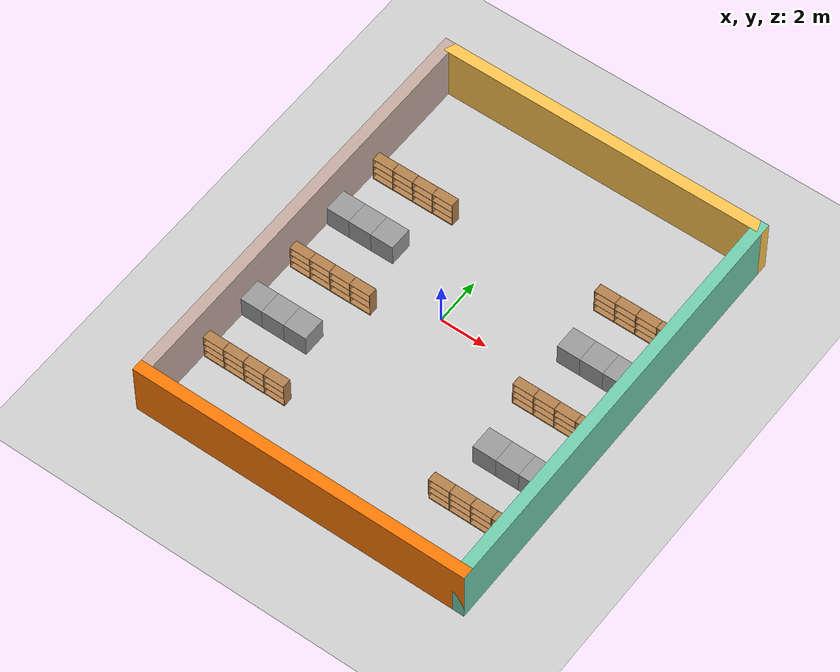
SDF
<sdf version="1.6">
 <world name="default">
  <light name="sun" type="directional">
   <pose>0 0 10 0 -0 0</pose>
   <diffuse>0.8 0.8 0.8 1</diffuse>
   <specular>0.2 0.2 0.2 1</specular>
   <attenuation>
    <range>1000</range>
    <constant>0.9</constant>
    <linear>0.01</linear>
    <quadratic>0.001</quadratic>
   </attenuation>
   <direction>-0.5 0.1 -0.9</direction>
  </light>
  <model name="ground_plane">
   <static>1</static>
   <link name="link">
    <collision name="collision">
     <geometry><plane><normal>0 0 1</normal><size>100 100</size></plane></geometry>
     <surface>
      <contact><collide_bitmask>65535</collide_bitmask></contact>
      <friction><ode><mu>100</mu><mu2>50</mu2></ode></friction>
     </surface>
    </collision>
    <visual name="visual">
     <cast_shadows>0</cast_shadows>
     <geometry><plane><normal>0 0 1</normal><size>100 100</size></plane></geometry>
     <material>
      <script><uri>file://media/materials/scripts/gazebo.material</uri><name>Gazebo/Grey</name></script>
     </material>
    </visual>
   </link>
  </model>
  <gravity>0 0 -9.8</gravity>
  <magnetic_field>6e-06 2.3e-05 -4.2e-05</magnetic_field>
  <atmosphere type="adiabatic"/>
  <physics name="default_physics" default="0" type="ode">
   <max_step_size>0.001</max_step_size>
   <real_time_factor>1</real_time_factor>
   <real_time_update_rate>1000</real_time_update_rate>
  </physics>
  <scene><ambient>0.4 0.4 0.4 1</ambient><background>0.7 0.7 0.7 1</background><shadows>1</shadows></scene>
  <spherical_coordinates>
   <surface_model>EARTH_WGS84</surface_model>
   <latitude_deg>0</latitude_deg>
   <longitude_deg>0</longitude_deg>
   <elevation>0</elevation>
   <heading_deg>0</heading_deg>
  </spherical_coordinates>
  <model name="shelf">
   <model name="bookshelf">
    <static>1</static>
    <link name="link">
     <inertial><mass>1</mass></inertial>
     <collision name="back">
      <pose>0 0.005 0.6 0 -0 0</pose>
      <geometry><box><size>0.9 0.01 1.2</size></box></geometry>
     </collision>
     <visual name="visual1">
      <pose>0 0.005 0.6 0 -0 0</pose>
      <geometry><box><size>0.9 0.01 1.2</size></box></geometry>
      <material>
       <script><uri>file://media/materials/scripts/gazebo.material</uri><name>Gazebo/Wood</name></script>
      </material>
     </visual>
     <collision name="left_side">
      <pose>0.45 -0.195 0.6 0 -0 0</pose>
      <geometry><box><size>0.02 0.4 1.2</size></box></geometry>
     </collision>
     <visual name="visual2">
      <pose>0.45 -0.195 0.6 0 -0 0</pose>
      <geometry><box><size>0.02 0.4 1.2</size></box></geometry>
      <material>
       <script><uri>file://media/materials/scripts/gazebo.material</uri><name>Gazebo/Wood</name></script>
      </material>
     </visual>
     <collision name="right_side">
      <pose>-0.45 -0.195 0.6 0 -0 0</pose>
      <geometry><box><size>0.02 0.4 1.2</size></box></geometry>
     </collision>
     <visual name="visual3">
      <pose>-0.45 -0.195 0.6 0 -0 0</pose>
      <geometry><box><size>0.02 0.4 1.2</size></box></geometry>
      <material>
       <script><uri>file://media/materials/scripts/gazebo.material</uri><name>Gazebo/Wood</name></script>
      </material>
     </visual>
     <collision name="bottom">
      <pose>0 -0.195 0.03 0 -0 0</pose>
      <geometry><box><size>0.88 0.4 0.06</size></box></geometry>
     </collision>
     <visual name="visual4">
      <pose>0 -0.195 0.03 0 -0 0</pose>
      <geometry><box><size>0.88 0.4 0.06</size></box></geometry>
      <material>
       <script><uri>file://media/materials/scripts/gazebo.material</uri><name>Gazebo/Wood</name></script>
      </material>
     </visual>
     <collision name="top">
      <pose>0 -0.195 1.19 0 -0 0</pose>
      <geometry><box><size>0.88 0.4 0.02</size></box></geometry>
     </collision>
     <visual name="visual5">
      <pose>0 -0.195 1.19 0 -0 0</pose>
      <geometry><box><size>0.88 0.4 0.02</size></box></geometry>
      <material>
       <script><uri>file://media/materials/scripts/gazebo.material</uri><name>Gazebo/Wood</name></script>
      </material>
     </visual>
     <collision name="low_shelf">
      <pose>0 -0.195 0.43 0 -0 0</pose>
      <geometry><box><size>0.88 0.4 0.02</size></box></geometry>
     </collision>
     <visual name="visual6">
      <pose>0 -0.195 0.43 0 -0 0</pose>
      <geometry><box><size>0.88 0.4 0.02</size></box></geometry>
      <material>
       <script><uri>file://media/materials/scripts/gazebo.material</uri><name>Gazebo/Wood</name></script>
      </material>
     </visual>
     <collision name="high_shelf">
      <pose>0 -0.195 0.8 0 -0 0</pose>
      <geometry><box><size>0.88 0.4 0.02</size></box></geometry>
     </collision>
     <visual name="visual7">
      <pose>0 -0.195 0.8 0 -0 0</pose>
      <geometry><box><size>0.88 0.4 0.02</size></box></geometry>
      <material>
       <script><uri>file://media/materials/scripts/gazebo.material</uri><name>Gazebo/Wood</name></script>
      </material>
     </visual>
    </link>
    <pose>-1.36031 -0.003398 0 0 -0 0</pose>
   </model>
   <model name="bookshelf_clone">
    <static>1</static>
    <link name="link">
     <inertial><mass>1</mass></inertial>
     <collision name="back">
      <pose>0 0.005 0.6 0 -0 0</pose>
      <geometry><box><size>0.9 0.01 1.2</size></box></geometry>
     </collision>
     <visual name="visual1">
      <pose>0 0.005 0.6 0 -0 0</pose>
      <geometry><box><size>0.9 0.01 1.2</size></box></geometry>
      <material>
       <script><uri>file://media/materials/scripts/gazebo.material</uri><name>Gazebo/Wood</name></script>
      </material>
     </visual>
     <collision name="left_side">
      <pose>0.45 -0.195 0.6 0 -0 0</pose>
      <geometry><box><size>0.02 0.4 1.2</size></box></geometry>
     </collision>
     <visual name="visual2">
      <pose>0.45 -0.195 0.6 0 -0 0</pose>
      <geometry><box><size>0.02 0.4 1.2</size></box></geometry>
      <material>
       <script><uri>file://media/materials/scripts/gazebo.material</uri><name>Gazebo/Wood</name></script>
      </material>
     </visual>
     <collision name="right_side">
      <pose>-0.45 -0.195 0.6 0 -0 0</pose>
      <geometry><box><size>0.02 0.4 1.2</size></box></geometry>
     </collision>
     <visual name="visual3">
      <pose>-0.45 -0.195 0.6 0 -0 0</pose>
      <geometry><box><size>0.02 0.4 1.2</size></box></geometry>
      <material>
       <script><uri>file://media/materials/scripts/gazebo.material</uri><name>Gazebo/Wood</name></script>
      </material>
     </visual>
     <collision name="bottom">
      <pose>0 -0.195 0.03 0 -0 0</pose>
      <geometry><box><size>0.88 0.4 0.06</size></box></geometry>
     </collision>
     <visual name="visual4">
      <pose>0 -0.195 0.03 0 -0 0</pose>
      <geometry><box><size>0.88 0.4 0.06</size></box></geometry>
      <material>
       <script><uri>file://media/materials/scripts/gazebo.material</uri><name>Gazebo/Wood</name></script>
      </material>
     </visual>
     <collision name="top">
      <pose>0 -0.195 1.19 0 -0 0</pose>
      <geometry><box><size>0.88 0.4 0.02</size></box></geometry>
     </collision>
     <visual name="visual5">
      <pose>0 -0.195 1.19 0 -0 0</pose>
      <geometry><box><size>0.88 0.4 0.02</size></box></geometry>
      <material>
       <script><uri>file://media/materials/scripts/gazebo.material</uri><name>Gazebo/Wood</name></script>
      </material>
     </visual>
     <collision name="low_shelf">
      <pose>0 -0.195 0.43 0 -0 0</pose>
      <geometry><box><size>0.88 0.4 0.02</size></box></geometry>
     </collision>
     <visual name="visual6">
      <pose>0 -0.195 0.43 0 -0 0</pose>
      <geometry><box><size>0.88 0.4 0.02</size></box></geometry>
      <material>
       <script><uri>file://media/materials/scripts/gazebo.material</uri><name>Gazebo/Wood</name></script>
      </material>
     </visual>
     <collision name="high_shelf">
      <pose>0 -0.195 0.8 0 -0 0</pose>
      <geometry><box><size>0.88 0.4 0.02</size></box></geometry>
     </collision>
     <visual name="visual7">
      <pose>0 -0.195 0.8 0 -0 0</pose>
      <geometry><box><size>0.88 0.4 0.02</size></box></geometry>
      <material>
       <script><uri>file://media/materials/scripts/gazebo.material</uri><name>Gazebo/Wood</name></script>
      </material>
     </visual>
    </link>
    <pose>-0.456544 -0.000114 0 0 -0 0</pose>
   </model>
   <model name="bookshelf_clone_clone">
    <static>1</static>
    <link name="link">
     <inertial><mass>1</mass></inertial>
     <collision name="back">
      <pose>0 0.005 0.6 0 -0 0</pose>
      <geometry><box><size>0.9 0.01 1.2</size></box></geometry>
     </collision>
     <visual name="visual1">
      <pose>0 0.005 0.6 0 -0 0</pose>
      <geometry><box><size>0.9 0.01 1.2</size></box></geometry>
      <material>
       <script><uri>file://media/materials/scripts/gazebo.material</uri><name>Gazebo/Wood</name></script>
      </material>
     </visual>
     <collision name="left_side">
      <pose>0.45 -0.195 0.6 0 -0 0</pose>
      <geometry><box><size>0.02 0.4 1.2</size></box></geometry>
     </collision>
     <visual name="visual2">
      <pose>0.45 -0.195 0.6 0 -0 0</pose>
      <geometry><box><size>0.02 0.4 1.2</size></box></geometry>
      <material>
       <script><uri>file://media/materials/scripts/gazebo.material</uri><name>Gazebo/Wood</name></script>
      </material>
     </visual>
     <collision name="right_side">
      <pose>-0.45 -0.195 0.6 0 -0 0</pose>
      <geometry><box><size>0.02 0.4 1.2</size></box></geometry>
     </collision>
     <visual name="visual3">
      <pose>-0.45 -0.195 0.6 0 -0 0</pose>
      <geometry><box><size>0.02 0.4 1.2</size></box></geometry>
      <material>
       <script><uri>file://media/materials/scripts/gazebo.material</uri><name>Gazebo/Wood</name></script>
      </material>
     </visual>
     <collision name="bottom">
      <pose>0 -0.195 0.03 0 -0 0</pose>
      <geometry><box><size>0.88 0.4 0.06</size></box></geometry>
     </collision>
     <visual name="visual4">
      <pose>0 -0.195 0.03 0 -0 0</pose>
      <geometry><box><size>0.88 0.4 0.06</size></box></geometry>
      <material>
       <script><uri>file://media/materials/scripts/gazebo.material</uri><name>Gazebo/Wood</name></script>
      </material>
     </visual>
     <collision name="top">
      <pose>0 -0.195 1.19 0 -0 0</pose>
      <geometry><box><size>0.88 0.4 0.02</size></box></geometry>
     </collision>
     <visual name="visual5">
      <pose>0 -0.195 1.19 0 -0 0</pose>
      <geometry><box><size>0.88 0.4 0.02</size></box></geometry>
      <material>
       <script><uri>file://media/materials/scripts/gazebo.material</uri><name>Gazebo/Wood</name></script>
      </material>
     </visual>
     <collision name="low_shelf">
      <pose>0 -0.195 0.43 0 -0 0</pose>
      <geometry><box><size>0.88 0.4 0.02</size></box></geometry>
     </collision>
     <visual name="visual6">
      <pose>0 -0.195 0.43 0 -0 0</pose>
      <geometry><box><size>0.88 0.4 0.02</size></box></geometry>
      <material>
       <script><uri>file://media/materials/scripts/gazebo.material</uri><name>Gazebo/Wood</name></script>
      </material>
     </visual>
     <collision name="high_shelf">
      <pose>0 -0.195 0.8 0 -0 0</pose>
      <geometry><box><size>0.88 0.4 0.02</size></box></geometry>
     </collision>
     <visual name="visual7">
      <pose>0 -0.195 0.8 0 -0 0</pose>
      <geometry><box><size>0.88 0.4 0.02</size></box></geometry>
      <material>
       <script><uri>file://media/materials/scripts/gazebo.material</uri><name>Gazebo/Wood</name></script>
      </material>
     </visual>
    </link>
    <pose>0.456143 -0.001997 0 0 -0 0</pose>
   </model>
   <model name="bookshelf_clone_clone_0">
    <static>1</static>
    <link name="link">
     <inertial><mass>1</mass></inertial>
     <collision name="back">
      <pose>0 0.005 0.6 0 -0 0</pose>
      <geometry><box><size>0.9 0.01 1.2</size></box></geometry>
     </collision>
     <visual name="visual1">
      <pose>0 0.005 0.6 0 -0 0</pose>
      <geometry><box><size>0.9 0.01 1.2</size></box></geometry>
      <material>
       <script><uri>file://media/materials/scripts/gazebo.material</uri><name>Gazebo/Wood</name></script>
      </material>
     </visual>
     <collision name="left_side">
      <pose>0.45 -0.195 0.6 0 -0 0</pose>
      <geometry><box><size>0.02 0.4 1.2</size></box></geometry>
     </collision>
     <visual name="visual2">
      <pose>0.45 -0.195 0.6 0 -0 0</pose>
      <geometry><box><size>0.02 0.4 1.2</size></box></geometry>
      <material>
       <script><uri>file://media/materials/scripts/gazebo.material</uri><name>Gazebo/Wood</name></script>
      </material>
     </visual>
     <collision name="right_side">
      <pose>-0.45 -0.195 0.6 0 -0 0</pose>
      <geometry><box><size>0.02 0.4 1.2</size></box></geometry>
     </collision>
     <visual name="visual3">
      <pose>-0.45 -0.195 0.6 0 -0 0</pose>
      <geometry><box><size>0.02 0.4 1.2</size></box></geometry>
      <material>
       <script><uri>file://media/materials/scripts/gazebo.material</uri><name>Gazebo/Wood</name></script>
      </material>
     </visual>
     <collision name="bottom">
      <pose>0 -0.195 0.03 0 -0 0</pose>
      <geometry><box><size>0.88 0.4 0.06</size></box></geometry>
     </collision>
     <visual name="visual4">
      <pose>0 -0.195 0.03 0 -0 0</pose>
      <geometry><box><size>0.88 0.4 0.06</size></box></geometry>
      <material>
       <script><uri>file://media/materials/scripts/gazebo.material</uri><name>Gazebo/Wood</name></script>
      </material>
     </visual>
     <collision name="top">
      <pose>0 -0.195 1.19 0 -0 0</pose>
      <geometry><box><size>0.88 0.4 0.02</size></box></geometry>
     </collision>
     <visual name="visual5">
      <pose>0 -0.195 1.19 0 -0 0</pose>
      <geometry><box><size>0.88 0.4 0.02</size></box></geometry>
      <material>
       <script><uri>file://media/materials/scripts/gazebo.material</uri><name>Gazebo/Wood</name></script>
      </material>
     </visual>
     <collision name="low_shelf">
      <pose>0 -0.195 0.43 0 -0 0</pose>
      <geometry><box><size>0.88 0.4 0.02</size></box></geometry>
     </collision>
     <visual name="visual6">
      <pose>0 -0.195 0.43 0 -0 0</pose>
      <geometry><box><size>0.88 0.4 0.02</size></box></geometry>
      <material>
       <script><uri>file://media/materials/scripts/gazebo.material</uri><name>Gazebo/Wood</name></script>
      </material>
     </visual>
     <collision name="high_shelf">
      <pose>0 -0.195 0.8 0 -0 0</pose>
      <geometry><box><size>0.88 0.4 0.02</size></box></geometry>
     </collision>
     <visual name="visual7">
      <pose>0 -0.195 0.8 0 -0 0</pose>
      <geometry><box><size>0.88 0.4 0.02</size></box></geometry>
      <material>
       <script><uri>file://media/materials/scripts/gazebo.material</uri><name>Gazebo/Wood</name></script>
      </material>
     </visual>
    </link>
    <pose>1.3607 0.005513 0 0 -0 0</pose>
   </model>
   <static>0</static>
   <pose>-4.07417 -5.95913 0 0 -0 0</pose>
  </model>
  <model name="thick_wall">
   <link name="Wall_0">
    <pose>0 -9 0 0 -0 0</pose>
    <inertial>
     <mass>100</mass>
     <inertia><ixx>1</ixx><ixy>0</ixy><ixz>0</ixz><iyy>1</iyy><iyz>0</iyz><izz>1</izz></inertia>
    </inertial>
    <visual name="Wall_0_Visual">
     <pose>0 0 1.25 0 -0 0</pose>
     <geometry><box><size>14.5 0.5 2.5</size></box></geometry>
     <material>
      <script><uri>file://media/materials/scripts/gazebo.material</uri><name>Gazebo/Grey</name></script>
      <ambient>0.996 0.475 0.02 1</ambient>
      <shader type="pixel"><normal_map>__default__</normal_map></shader>
      <diffuse>0.7 0.7 0.7 1</diffuse>
      <specular>0.01 0.01 0.01 1</specular>
      <emissive>0 0 0 1</emissive>
     </material>
     <meta><layer>0</layer></meta>
    </visual>
    <collision name="Wall_0_Collision">
     <pose>0 0 1.25 0 -0 0</pose>
     <geometry><box><size>14.5 0.5 2.5</size></box></geometry>
     <surface>
      <friction>
       <ode><mu>1</mu><mu2>1</mu2><fdir1>0 0 0</fdir1><slip1>0</slip1><slip2>0</slip2></ode>
       <torsional>
        <coefficient>1</coefficient>
        <patch_radius>0</patch_radius>
        <surface_radius>0</surface_radius>
        <use_patch_radius>1</use_patch_radius>
        <ode><slip>0</slip></ode>
       </torsional>
      </friction>
      <bounce><restitution_coefficient>0</restitution_coefficient><threshold>1e+06</threshold></bounce>
      <contact>
       <collide_without_contact>0</collide_without_contact>
       <collide_without_contact_bitmask>1</collide_without_contact_bitmask>
       <collide_bitmask>1</collide_bitmask>
       <ode>
        <soft_cfm>0</soft_cfm>
        <soft_erp>0.2</soft_erp>
        <kp>1e+13</kp>
        <kd>1</kd>
        <max_vel>0.01</max_vel>
        <min_depth>0</min_depth>
       </ode>
       <bullet>
        <split_impulse>1</split_impulse>
        <split_impulse_penetration_threshold>-0.01</split_impulse_penetration_threshold>
        <soft_cfm>0</soft_cfm>
        <soft_erp>0.2</soft_erp>
        <kp>1e+13</kp>
        <kd>1</kd>
       </bullet>
      </contact>
     </surface>
    </collision>
   </link>
   <link name="Wall_1">
    <pose>7 0 0 0 -0 1.5708</pose>
    <inertial>
     <mass>100</mass>
     <inertia><ixx>1</ixx><ixy>0</ixy><ixz>0</ixz><iyy>1</iyy><iyz>0</iyz><izz>1</izz></inertia>
    </inertial>
    <visual name="Wall_1_Visual">
     <pose>0 0 1.25 0 -0 0</pose>
     <geometry><box><size>18.5 0.5 2.5</size></box></geometry>
     <material>
      <script><uri>file://media/materials/scripts/gazebo.material</uri><name>Gazebo/Grey</name></script>
      <ambient>0.435 0.796 0.675 1</ambient>
      <shader type="pixel"><normal_map>__default__</normal_map></shader>
      <diffuse>0.7 0.7 0.7 1</diffuse>
      <specular>0.01 0.01 0.01 1</specular>
      <emissive>0 0 0 1</emissive>
     </material>
     <meta><layer>0</layer></meta>
    </visual>
    <collision name="Wall_1_Collision">
     <pose>0 0 1.25 0 -0 0</pose>
     <geometry><box><size>18.5 0.5 2.5</size></box></geometry>
     <surface>
      <friction>
       <ode><mu>1</mu><mu2>1</mu2><fdir1>0 0 0</fdir1><slip1>0</slip1><slip2>0</slip2></ode>
       <torsional>
        <coefficient>1</coefficient>
        <patch_radius>0</patch_radius>
        <surface_radius>0</surface_radius>
        <use_patch_radius>1</use_patch_radius>
        <ode><slip>0</slip></ode>
       </torsional>
      </friction>
      <bounce><restitution_coefficient>0</restitution_coefficient><threshold>1e+06</threshold></bounce>
      <contact>
       <collide_without_contact>0</collide_without_contact>
       <collide_without_contact_bitmask>1</collide_without_contact_bitmask>
       <collide_bitmask>1</collide_bitmask>
       <ode>
        <soft_cfm>0</soft_cfm>
        <soft_erp>0.2</soft_erp>
        <kp>1e+13</kp>
        <kd>1</kd>
        <max_vel>0.01</max_vel>
        <min_depth>0</min_depth>
       </ode>
       <bullet>
        <split_impulse>1</split_impulse>
        <split_impulse_penetration_threshold>-0.01</split_impulse_penetration_threshold>
        <soft_cfm>0</soft_cfm>
        <soft_erp>0.2</soft_erp>
        <kp>1e+13</kp>
        <kd>1</kd>
       </bullet>
      </contact>
     </surface>
    </collision>
   </link>
   <link name="Wall_2">
    <pose>0 9 0 0 -0 3.14159</pose>
    <inertial>
     <mass>100</mass>
     <inertia><ixx>1</ixx><ixy>0</ixy><ixz>0</ixz><iyy>1</iyy><iyz>0</iyz><izz>1</izz></inertia>
    </inertial>
    <visual name="Wall_2_Visual">
     <pose>0 0 1.25 0 -0 0</pose>
     <geometry><box><size>14.5 0.5 2.5</size></box></geometry>
     <material>
      <script><uri>file://media/materials/scripts/gazebo.material</uri><name>Gazebo/Grey</name></script>
      <ambient>1 0.765 0.306 1</ambient>
      <shader type="pixel"><normal_map>__default__</normal_map></shader>
      <diffuse>0.7 0.7 0.7 1</diffuse>
      <specular>0.01 0.01 0.01 1</specular>
      <emissive>0 0 0 1</emissive>
     </material>
     <meta><layer>0</layer></meta>
    </visual>
    <collision name="Wall_2_Collision">
     <pose>0 0 1.25 0 -0 0</pose>
     <geometry><box><size>14.5 0.5 2.5</size></box></geometry>
     <surface>
      <friction>
       <ode><mu>1</mu><mu2>1</mu2><fdir1>0 0 0</fdir1><slip1>0</slip1><slip2>0</slip2></ode>
       <torsional>
        <coefficient>1</coefficient>
        <patch_radius>0</patch_radius>
        <surface_radius>0</surface_radius>
        <use_patch_radius>1</use_patch_radius>
        <ode><slip>0</slip></ode>
       </torsional>
      </friction>
      <bounce><restitution_coefficient>0</restitution_coefficient><threshold>1e+06</threshold></bounce>
      <contact>
       <collide_without_contact>0</collide_without_contact>
       <collide_without_contact_bitmask>1</collide_without_contact_bitmask>
       <collide_bitmask>1</collide_bitmask>
       <ode>
        <soft_cfm>0</soft_cfm>
        <soft_erp>0.2</soft_erp>
        <kp>1e+13</kp>
        <kd>1</kd>
        <max_vel>0.01</max_vel>
        <min_depth>0</min_depth>
       </ode>
       <bullet>
        <split_impulse>1</split_impulse>
        <split_impulse_penetration_threshold>-0.01</split_impulse_penetration_threshold>
        <soft_cfm>0</soft_cfm>
        <soft_erp>0.2</soft_erp>
        <kp>1e+13</kp>
        <kd>1</kd>
       </bullet>
      </contact>
     </surface>
    </collision>
   </link>
   <link name="Wall_3">
    <pose>-7 0 0 0 0 -1.5708</pose>
    <inertial>
     <mass>100</mass>
     <inertia><ixx>1</ixx><ixy>0</ixy><ixz>0</ixz><iyy>1</iyy><iyz>0</iyz><izz>1</izz></inertia>
    </inertial>
    <visual name="Wall_3_Visual">
     <pose>0 0 1.25 0 -0 0</pose>
     <geometry><box><size>18.5 0.5 2.5</size></box></geometry>
     <material>
      <script><uri>file://media/materials/scripts/gazebo.material</uri><name>Gazebo/Grey</name></script>
      <ambient>0.761 0.663 0.627 1</ambient>
      <shader type="pixel"><normal_map>__default__</normal_map></shader>
      <diffuse>0.7 0.7 0.7 1</diffuse>
      <specular>0.01 0.01 0.01 1</specular>
      <emissive>0 0 0 1</emissive>
     </material>
     <meta><layer>0</layer></meta>
    </visual>
    <collision name="Wall_3_Collision">
     <pose>0 0 1.25 0 -0 0</pose>
     <geometry><box><size>18.5 0.5 2.5</size></box></geometry>
     <surface>
      <friction>
       <ode><mu>1</mu><mu2>1</mu2><fdir1>0 0 0</fdir1><slip1>0</slip1><slip2>0</slip2></ode>
       <torsional>
        <coefficient>1</coefficient>
        <patch_radius>0</patch_radius>
        <surface_radius>0</surface_radius>
        <use_patch_radius>1</use_patch_radius>
        <ode><slip>0</slip></ode>
       </torsional>
      </friction>
      <bounce><restitution_coefficient>0</restitution_coefficient><threshold>1e+06</threshold></bounce>
      <contact>
       <collide_without_contact>0</collide_without_contact>
       <collide_without_contact_bitmask>1</collide_without_contact_bitmask>
       <collide_bitmask>1</collide_bitmask>
       <ode>
        <soft_cfm>0</soft_cfm>
        <soft_erp>0.2</soft_erp>
        <kp>1e+13</kp>
        <kd>1</kd>
        <max_vel>0.01</max_vel>
        <min_depth>0</min_depth>
       </ode>
       <bullet>
        <split_impulse>1</split_impulse>
        <split_impulse_penetration_threshold>-0.01</split_impulse_penetration_threshold>
        <soft_cfm>0</soft_cfm>
        <soft_erp>0.2</soft_erp>
        <kp>1e+13</kp>
        <kd>1</kd>
       </bullet>
      </contact>
     </surface>
    </collision>
   </link>
   <static>1</static>
   <pose>0.816557 -0.3056 0 0 -0 0</pose>
  </model>
  <model name="shelf_clone">
   <model name="bookshelf">
    <static>1</static>
    <link name="link">
     <inertial><mass>1</mass></inertial>
     <collision name="back">
      <pose>0 0.005 0.6 0 -0 0</pose>
      <geometry><box><size>0.9 0.01 1.2</size></box></geometry>
     </collision>
     <visual name="visual1">
      <pose>0 0.005 0.6 0 -0 0</pose>
      <geometry><box><size>0.9 0.01 1.2</size></box></geometry>
      <material>
       <script><uri>file://media/materials/scripts/gazebo.material</uri><name>Gazebo/Wood</name></script>
      </material>
     </visual>
     <collision name="left_side">
      <pose>0.45 -0.195 0.6 0 -0 0</pose>
      <geometry><box><size>0.02 0.4 1.2</size></box></geometry>
     </collision>
     <visual name="visual2">
      <pose>0.45 -0.195 0.6 0 -0 0</pose>
      <geometry><box><size>0.02 0.4 1.2</size></box></geometry>
      <material>
       <script><uri>file://media/materials/scripts/gazebo.material</uri><name>Gazebo/Wood</name></script>
      </material>
     </visual>
     <collision name="right_side">
      <pose>-0.45 -0.195 0.6 0 -0 0</pose>
      <geometry><box><size>0.02 0.4 1.2</size></box></geometry>
     </collision>
     <visual name="visual3">
      <pose>-0.45 -0.195 0.6 0 -0 0</pose>
      <geometry><box><size>0.02 0.4 1.2</size></box></geometry>
      <material>
       <script><uri>file://media/materials/scripts/gazebo.material</uri><name>Gazebo/Wood</name></script>
      </material>
     </visual>
     <collision name="bottom">
      <pose>0 -0.195 0.03 0 -0 0</pose>
      <geometry><box><size>0.88 0.4 0.06</size></box></geometry>
     </collision>
     <visual name="visual4">
      <pose>0 -0.195 0.03 0 -0 0</pose>
      <geometry><box><size>0.88 0.4 0.06</size></box></geometry>
      <material>
       <script><uri>file://media/materials/scripts/gazebo.material</uri><name>Gazebo/Wood</name></script>
      </material>
     </visual>
     <collision name="top">
      <pose>0 -0.195 1.19 0 -0 0</pose>
      <geometry><box><size>0.88 0.4 0.02</size></box></geometry>
     </collision>
     <visual name="visual5">
      <pose>0 -0.195 1.19 0 -0 0</pose>
      <geometry><box><size>0.88 0.4 0.02</size></box></geometry>
      <material>
       <script><uri>file://media/materials/scripts/gazebo.material</uri><name>Gazebo/Wood</name></script>
      </material>
     </visual>
     <collision name="low_shelf">
      <pose>0 -0.195 0.43 0 -0 0</pose>
      <geometry><box><size>0.88 0.4 0.02</size></box></geometry>
     </collision>
     <visual name="visual6">
      <pose>0 -0.195 0.43 0 -0 0</pose>
      <geometry><box><size>0.88 0.4 0.02</size></box></geometry>
      <material>
       <script><uri>file://media/materials/scripts/gazebo.material</uri><name>Gazebo/Wood</name></script>
      </material>
     </visual>
     <collision name="high_shelf">
      <pose>0 -0.195 0.8 0 -0 0</pose>
      <geometry><box><size>0.88 0.4 0.02</size></box></geometry>
     </collision>
     <visual name="visual7">
      <pose>0 -0.195 0.8 0 -0 0</pose>
      <geometry><box><size>0.88 0.4 0.02</size></box></geometry>
      <material>
       <script><uri>file://media/materials/scripts/gazebo.material</uri><name>Gazebo/Wood</name></script>
      </material>
     </visual>
    </link>
    <pose>-1.36031 -0.003398 0 0 -0 0</pose>
   </model>
   <model name="bookshelf_clone">
    <static>1</static>
    <link name="link">
     <inertial><mass>1</mass></inertial>
     <collision name="back">
      <pose>0 0.005 0.6 0 -0 0</pose>
      <geometry><box><size>0.9 0.01 1.2</size></box></geometry>
     </collision>
     <visual name="visual1">
      <pose>0 0.005 0.6 0 -0 0</pose>
      <geometry><box><size>0.9 0.01 1.2</size></box></geometry>
      <material>
       <script><uri>file://media/materials/scripts/gazebo.material</uri><name>Gazebo/Wood</name></script>
      </material>
     </visual>
     <collision name="left_side">
      <pose>0.45 -0.195 0.6 0 -0 0</pose>
      <geometry><box><size>0.02 0.4 1.2</size></box></geometry>
     </collision>
     <visual name="visual2">
      <pose>0.45 -0.195 0.6 0 -0 0</pose>
      <geometry><box><size>0.02 0.4 1.2</size></box></geometry>
      <material>
       <script><uri>file://media/materials/scripts/gazebo.material</uri><name>Gazebo/Wood</name></script>
      </material>
     </visual>
     <collision name="right_side">
      <pose>-0.45 -0.195 0.6 0 -0 0</pose>
      <geometry><box><size>0.02 0.4 1.2</size></box></geometry>
     </collision>
     <visual name="visual3">
      <pose>-0.45 -0.195 0.6 0 -0 0</pose>
      <geometry><box><size>0.02 0.4 1.2</size></box></geometry>
      <material>
       <script><uri>file://media/materials/scripts/gazebo.material</uri><name>Gazebo/Wood</name></script>
      </material>
     </visual>
     <collision name="bottom">
      <pose>0 -0.195 0.03 0 -0 0</pose>
      <geometry><box><size>0.88 0.4 0.06</size></box></geometry>
     </collision>
     <visual name="visual4">
      <pose>0 -0.195 0.03 0 -0 0</pose>
      <geometry><box><size>0.88 0.4 0.06</size></box></geometry>
      <material>
       <script><uri>file://media/materials/scripts/gazebo.material</uri><name>Gazebo/Wood</name></script>
      </material>
     </visual>
     <collision name="top">
      <pose>0 -0.195 1.19 0 -0 0</pose>
      <geometry><box><size>0.88 0.4 0.02</size></box></geometry>
     </collision>
     <visual name="visual5">
      <pose>0 -0.195 1.19 0 -0 0</pose>
      <geometry><box><size>0.88 0.4 0.02</size></box></geometry>
      <material>
       <script><uri>file://media/materials/scripts/gazebo.material</uri><name>Gazebo/Wood</name></script>
      </material>
     </visual>
     <collision name="low_shelf">
      <pose>0 -0.195 0.43 0 -0 0</pose>
      <geometry><box><size>0.88 0.4 0.02</size></box></geometry>
     </collision>
     <visual name="visual6">
      <pose>0 -0.195 0.43 0 -0 0</pose>
      <geometry><box><size>0.88 0.4 0.02</size></box></geometry>
      <material>
       <script><uri>file://media/materials/scripts/gazebo.material</uri><name>Gazebo/Wood</name></script>
      </material>
     </visual>
     <collision name="high_shelf">
      <pose>0 -0.195 0.8 0 -0 0</pose>
      <geometry><box><size>0.88 0.4 0.02</size></box></geometry>
     </collision>
     <visual name="visual7">
      <pose>0 -0.195 0.8 0 -0 0</pose>
      <geometry><box><size>0.88 0.4 0.02</size></box></geometry>
      <material>
       <script><uri>file://media/materials/scripts/gazebo.material</uri><name>Gazebo/Wood</name></script>
      </material>
     </visual>
    </link>
    <pose>-0.456544 -0.000114 0 0 -0 0</pose>
   </model>
   <model name="bookshelf_clone_clone">
    <static>1</static>
    <link name="link">
     <inertial><mass>1</mass></inertial>
     <collision name="back">
      <pose>0 0.005 0.6 0 -0 0</pose>
      <geometry><box><size>0.9 0.01 1.2</size></box></geometry>
     </collision>
     <visual name="visual1">
      <pose>0 0.005 0.6 0 -0 0</pose>
      <geometry><box><size>0.9 0.01 1.2</size></box></geometry>
      <material>
       <script><uri>file://media/materials/scripts/gazebo.material</uri><name>Gazebo/Wood</name></script>
      </material>
     </visual>
     <collision name="left_side">
      <pose>0.45 -0.195 0.6 0 -0 0</pose>
      <geometry><box><size>0.02 0.4 1.2</size></box></geometry>
     </collision>
     <visual name="visual2">
      <pose>0.45 -0.195 0.6 0 -0 0</pose>
      <geometry><box><size>0.02 0.4 1.2</size></box></geometry>
      <material>
       <script><uri>file://media/materials/scripts/gazebo.material</uri><name>Gazebo/Wood</name></script>
      </material>
     </visual>
     <collision name="right_side">
      <pose>-0.45 -0.195 0.6 0 -0 0</pose>
      <geometry><box><size>0.02 0.4 1.2</size></box></geometry>
     </collision>
     <visual name="visual3">
      <pose>-0.45 -0.195 0.6 0 -0 0</pose>
      <geometry><box><size>0.02 0.4 1.2</size></box></geometry>
      <material>
       <script><uri>file://media/materials/scripts/gazebo.material</uri><name>Gazebo/Wood</name></script>
      </material>
     </visual>
     <collision name="bottom">
      <pose>0 -0.195 0.03 0 -0 0</pose>
      <geometry><box><size>0.88 0.4 0.06</size></box></geometry>
     </collision>
     <visual name="visual4">
      <pose>0 -0.195 0.03 0 -0 0</pose>
      <geometry><box><size>0.88 0.4 0.06</size></box></geometry>
      <material>
       <script><uri>file://media/materials/scripts/gazebo.material</uri><name>Gazebo/Wood</name></script>
      </material>
     </visual>
     <collision name="top">
      <pose>0 -0.195 1.19 0 -0 0</pose>
      <geometry><box><size>0.88 0.4 0.02</size></box></geometry>
     </collision>
     <visual name="visual5">
      <pose>0 -0.195 1.19 0 -0 0</pose>
      <geometry><box><size>0.88 0.4 0.02</size></box></geometry>
      <material>
       <script><uri>file://media/materials/scripts/gazebo.material</uri><name>Gazebo/Wood</name></script>
      </material>
     </visual>
     <collision name="low_shelf">
      <pose>0 -0.195 0.43 0 -0 0</pose>
      <geometry><box><size>0.88 0.4 0.02</size></box></geometry>
     </collision>
     <visual name="visual6">
      <pose>0 -0.195 0.43 0 -0 0</pose>
      <geometry><box><size>0.88 0.4 0.02</size></box></geometry>
      <material>
       <script><uri>file://media/materials/scripts/gazebo.material</uri><name>Gazebo/Wood</name></script>
      </material>
     </visual>
     <collision name="high_shelf">
      <pose>0 -0.195 0.8 0 -0 0</pose>
      <geometry><box><size>0.88 0.4 0.02</size></box></geometry>
     </collision>
     <visual name="visual7">
      <pose>0 -0.195 0.8 0 -0 0</pose>
      <geometry><box><size>0.88 0.4 0.02</size></box></geometry>
      <material>
       <script><uri>file://media/materials/scripts/gazebo.material</uri><name>Gazebo/Wood</name></script>
      </material>
     </visual>
    </link>
    <pose>0.456143 -0.001997 0 0 -0 0</pose>
   </model>
   <model name="bookshelf_clone_clone_0">
    <static>1</static>
    <link name="link">
     <inertial><mass>1</mass></inertial>
     <collision name="back">
      <pose>0 0.005 0.6 0 -0 0</pose>
      <geometry><box><size>0.9 0.01 1.2</size></box></geometry>
     </collision>
     <visual name="visual1">
      <pose>0 0.005 0.6 0 -0 0</pose>
      <geometry><box><size>0.9 0.01 1.2</size></box></geometry>
      <material>
       <script><uri>file://media/materials/scripts/gazebo.material</uri><name>Gazebo/Wood</name></script>
      </material>
     </visual>
     <collision name="left_side">
      <pose>0.45 -0.195 0.6 0 -0 0</pose>
      <geometry><box><size>0.02 0.4 1.2</size></box></geometry>
     </collision>
     <visual name="visual2">
      <pose>0.45 -0.195 0.6 0 -0 0</pose>
      <geometry><box><size>0.02 0.4 1.2</size></box></geometry>
      <material>
       <script><uri>file://media/materials/scripts/gazebo.material</uri><name>Gazebo/Wood</name></script>
      </material>
     </visual>
     <collision name="right_side">
      <pose>-0.45 -0.195 0.6 0 -0 0</pose>
      <geometry><box><size>0.02 0.4 1.2</size></box></geometry>
     </collision>
     <visual name="visual3">
      <pose>-0.45 -0.195 0.6 0 -0 0</pose>
      <geometry><box><size>0.02 0.4 1.2</size></box></geometry>
      <material>
       <script><uri>file://media/materials/scripts/gazebo.material</uri><name>Gazebo/Wood</name></script>
      </material>
     </visual>
     <collision name="bottom">
      <pose>0 -0.195 0.03 0 -0 0</pose>
      <geometry><box><size>0.88 0.4 0.06</size></box></geometry>
     </collision>
     <visual name="visual4">
      <pose>0 -0.195 0.03 0 -0 0</pose>
      <geometry><box><size>0.88 0.4 0.06</size></box></geometry>
      <material>
       <script><uri>file://media/materials/scripts/gazebo.material</uri><name>Gazebo/Wood</name></script>
      </material>
     </visual>
     <collision name="top">
      <pose>0 -0.195 1.19 0 -0 0</pose>
      <geometry><box><size>0.88 0.4 0.02</size></box></geometry>
     </collision>
     <visual name="visual5">
      <pose>0 -0.195 1.19 0 -0 0</pose>
      <geometry><box><size>0.88 0.4 0.02</size></box></geometry>
      <material>
       <script><uri>file://media/materials/scripts/gazebo.material</uri><name>Gazebo/Wood</name></script>
      </material>
     </visual>
     <collision name="low_shelf">
      <pose>0 -0.195 0.43 0 -0 0</pose>
      <geometry><box><size>0.88 0.4 0.02</size></box></geometry>
     </collision>
     <visual name="visual6">
      <pose>0 -0.195 0.43 0 -0 0</pose>
      <geometry><box><size>0.88 0.4 0.02</size></box></geometry>
      <material>
       <script><uri>file://media/materials/scripts/gazebo.material</uri><name>Gazebo/Wood</name></script>
      </material>
     </visual>
     <collision name="high_shelf">
      <pose>0 -0.195 0.8 0 -0 0</pose>
      <geometry><box><size>0.88 0.4 0.02</size></box></geometry>
     </collision>
     <visual name="visual7">
      <pose>0 -0.195 0.8 0 -0 0</pose>
      <geometry><box><size>0.88 0.4 0.02</size></box></geometry>
      <material>
       <script><uri>file://media/materials/scripts/gazebo.material</uri><name>Gazebo/Wood</name></script>
      </material>
     </visual>
    </link>
    <pose>1.3607 0.005513 0 0 -0 0</pose>
   </model>
   <static>0</static>
   <pose>-4 -1 0 0 -0 0</pose>
  </model>
  <model name="shelf_clone_clone">
   <model name="bookshelf">
    <static>1</static>
    <link name="link">
     <inertial><mass>1</mass></inertial>
     <collision name="back">
      <pose>0 0.005 0.6 0 -0 0</pose>
      <geometry><box><size>0.9 0.01 1.2</size></box></geometry>
     </collision>
     <visual name="visual1">
      <pose>0 0.005 0.6 0 -0 0</pose>
      <geometry><box><size>0.9 0.01 1.2</size></box></geometry>
      <material>
       <script><uri>file://media/materials/scripts/gazebo.material</uri><name>Gazebo/Wood</name></script>
      </material>
     </visual>
     <collision name="left_side">
      <pose>0.45 -0.195 0.6 0 -0 0</pose>
      <geometry><box><size>0.02 0.4 1.2</size></box></geometry>
     </collision>
     <visual name="visual2">
      <pose>0.45 -0.195 0.6 0 -0 0</pose>
      <geometry><box><size>0.02 0.4 1.2</size></box></geometry>
      <material>
       <script><uri>file://media/materials/scripts/gazebo.material</uri><name>Gazebo/Wood</name></script>
      </material>
     </visual>
     <collision name="right_side">
      <pose>-0.45 -0.195 0.6 0 -0 0</pose>
      <geometry><box><size>0.02 0.4 1.2</size></box></geometry>
     </collision>
     <visual name="visual3">
      <pose>-0.45 -0.195 0.6 0 -0 0</pose>
      <geometry><box><size>0.02 0.4 1.2</size></box></geometry>
      <material>
       <script><uri>file://media/materials/scripts/gazebo.material</uri><name>Gazebo/Wood</name></script>
      </material>
     </visual>
     <collision name="bottom">
      <pose>0 -0.195 0.03 0 -0 0</pose>
      <geometry><box><size>0.88 0.4 0.06</size></box></geometry>
     </collision>
     <visual name="visual4">
      <pose>0 -0.195 0.03 0 -0 0</pose>
      <geometry><box><size>0.88 0.4 0.06</size></box></geometry>
      <material>
       <script><uri>file://media/materials/scripts/gazebo.material</uri><name>Gazebo/Wood</name></script>
      </material>
     </visual>
     <collision name="top">
      <pose>0 -0.195 1.19 0 -0 0</pose>
      <geometry><box><size>0.88 0.4 0.02</size></box></geometry>
     </collision>
     <visual name="visual5">
      <pose>0 -0.195 1.19 0 -0 0</pose>
      <geometry><box><size>0.88 0.4 0.02</size></box></geometry>
      <material>
       <script><uri>file://media/materials/scripts/gazebo.material</uri><name>Gazebo/Wood</name></script>
      </material>
     </visual>
     <collision name="low_shelf">
      <pose>0 -0.195 0.43 0 -0 0</pose>
      <geometry><box><size>0.88 0.4 0.02</size></box></geometry>
     </collision>
     <visual name="visual6">
      <pose>0 -0.195 0.43 0 -0 0</pose>
      <geometry><box><size>0.88 0.4 0.02</size></box></geometry>
      <material>
       <script><uri>file://media/materials/scripts/gazebo.material</uri><name>Gazebo/Wood</name></script>
      </material>
     </visual>
     <collision name="high_shelf">
      <pose>0 -0.195 0.8 0 -0 0</pose>
      <geometry><box><size>0.88 0.4 0.02</size></box></geometry>
     </collision>
     <visual name="visual7">
      <pose>0 -0.195 0.8 0 -0 0</pose>
      <geometry><box><size>0.88 0.4 0.02</size></box></geometry>
      <material>
       <script><uri>file://media/materials/scripts/gazebo.material</uri><name>Gazebo/Wood</name></script>
      </material>
     </visual>
    </link>
    <pose>-1.36031 -0.003398 0 0 -0 0</pose>
   </model>
   <model name="bookshelf_clone">
    <static>1</static>
    <link name="link">
     <inertial><mass>1</mass></inertial>
     <collision name="back">
      <pose>0 0.005 0.6 0 -0 0</pose>
      <geometry><box><size>0.9 0.01 1.2</size></box></geometry>
     </collision>
     <visual name="visual1">
      <pose>0 0.005 0.6 0 -0 0</pose>
      <geometry><box><size>0.9 0.01 1.2</size></box></geometry>
      <material>
       <script><uri>file://media/materials/scripts/gazebo.material</uri><name>Gazebo/Wood</name></script>
      </material>
     </visual>
     <collision name="left_side">
      <pose>0.45 -0.195 0.6 0 -0 0</pose>
      <geometry><box><size>0.02 0.4 1.2</size></box></geometry>
     </collision>
     <visual name="visual2">
      <pose>0.45 -0.195 0.6 0 -0 0</pose>
      <geometry><box><size>0.02 0.4 1.2</size></box></geometry>
      <material>
       <script><uri>file://media/materials/scripts/gazebo.material</uri><name>Gazebo/Wood</name></script>
      </material>
     </visual>
     <collision name="right_side">
      <pose>-0.45 -0.195 0.6 0 -0 0</pose>
      <geometry><box><size>0.02 0.4 1.2</size></box></geometry>
     </collision>
     <visual name="visual3">
      <pose>-0.45 -0.195 0.6 0 -0 0</pose>
      <geometry><box><size>0.02 0.4 1.2</size></box></geometry>
      <material>
       <script><uri>file://media/materials/scripts/gazebo.material</uri><name>Gazebo/Wood</name></script>
      </material>
     </visual>
     <collision name="bottom">
      <pose>0 -0.195 0.03 0 -0 0</pose>
      <geometry><box><size>0.88 0.4 0.06</size></box></geometry>
     </collision>
     <visual name="visual4">
      <pose>0 -0.195 0.03 0 -0 0</pose>
      <geometry><box><size>0.88 0.4 0.06</size></box></geometry>
      <material>
       <script><uri>file://media/materials/scripts/gazebo.material</uri><name>Gazebo/Wood</name></script>
      </material>
     </visual>
     <collision name="top">
      <pose>0 -0.195 1.19 0 -0 0</pose>
      <geometry><box><size>0.88 0.4 0.02</size></box></geometry>
     </collision>
     <visual name="visual5">
      <pose>0 -0.195 1.19 0 -0 0</pose>
      <geometry><box><size>0.88 0.4 0.02</size></box></geometry>
      <material>
       <script><uri>file://media/materials/scripts/gazebo.material</uri><name>Gazebo/Wood</name></script>
      </material>
     </visual>
     <collision name="low_shelf">
      <pose>0 -0.195 0.43 0 -0 0</pose>
      <geometry><box><size>0.88 0.4 0.02</size></box></geometry>
     </collision>
     <visual name="visual6">
      <pose>0 -0.195 0.43 0 -0 0</pose>
      <geometry><box><size>0.88 0.4 0.02</size></box></geometry>
      <material>
       <script><uri>file://media/materials/scripts/gazebo.material</uri><name>Gazebo/Wood</name></script>
      </material>
     </visual>
     <collision name="high_shelf">
      <pose>0 -0.195 0.8 0 -0 0</pose>
      <geometry><box><size>0.88 0.4 0.02</size></box></geometry>
     </collision>
     <visual name="visual7">
      <pose>0 -0.195 0.8 0 -0 0</pose>
      <geometry><box><size>0.88 0.4 0.02</size></box></geometry>
      <material>
       <script><uri>file://media/materials/scripts/gazebo.material</uri><name>Gazebo/Wood</name></script>
      </material>
     </visual>
    </link>
    <pose>-0.456544 -0.000114 0 0 -0 0</pose>
   </model>
   <model name="bookshelf_clone_clone">
    <static>1</static>
    <link name="link">
     <inertial><mass>1</mass></inertial>
     <collision name="back">
      <pose>0 0.005 0.6 0 -0 0</pose>
      <geometry><box><size>0.9 0.01 1.2</size></box></geometry>
     </collision>
     <visual name="visual1">
      <pose>0 0.005 0.6 0 -0 0</pose>
      <geometry><box><size>0.9 0.01 1.2</size></box></geometry>
      <material>
       <script><uri>file://media/materials/scripts/gazebo.material</uri><name>Gazebo/Wood</name></script>
      </material>
     </visual>
     <collision name="left_side">
      <pose>0.45 -0.195 0.6 0 -0 0</pose>
      <geometry><box><size>0.02 0.4 1.2</size></box></geometry>
     </collision>
     <visual name="visual2">
      <pose>0.45 -0.195 0.6 0 -0 0</pose>
      <geometry><box><size>0.02 0.4 1.2</size></box></geometry>
      <material>
       <script><uri>file://media/materials/scripts/gazebo.material</uri><name>Gazebo/Wood</name></script>
      </material>
     </visual>
     <collision name="right_side">
      <pose>-0.45 -0.195 0.6 0 -0 0</pose>
      <geometry><box><size>0.02 0.4 1.2</size></box></geometry>
     </collision>
     <visual name="visual3">
      <pose>-0.45 -0.195 0.6 0 -0 0</pose>
      <geometry><box><size>0.02 0.4 1.2</size></box></geometry>
      <material>
       <script><uri>file://media/materials/scripts/gazebo.material</uri><name>Gazebo/Wood</name></script>
      </material>
     </visual>
     <collision name="bottom">
      <pose>0 -0.195 0.03 0 -0 0</pose>
      <geometry><box><size>0.88 0.4 0.06</size></box></geometry>
     </collision>
     <visual name="visual4">
      <pose>0 -0.195 0.03 0 -0 0</pose>
      <geometry><box><size>0.88 0.4 0.06</size></box></geometry>
      <material>
       <script><uri>file://media/materials/scripts/gazebo.material</uri><name>Gazebo/Wood</name></script>
      </material>
     </visual>
     <collision name="top">
      <pose>0 -0.195 1.19 0 -0 0</pose>
      <geometry><box><size>0.88 0.4 0.02</size></box></geometry>
     </collision>
     <visual name="visual5">
      <pose>0 -0.195 1.19 0 -0 0</pose>
      <geometry><box><size>0.88 0.4 0.02</size></box></geometry>
      <material>
       <script><uri>file://media/materials/scripts/gazebo.material</uri><name>Gazebo/Wood</name></script>
      </material>
     </visual>
     <collision name="low_shelf">
      <pose>0 -0.195 0.43 0 -0 0</pose>
      <geometry><box><size>0.88 0.4 0.02</size></box></geometry>
     </collision>
     <visual name="visual6">
      <pose>0 -0.195 0.43 0 -0 0</pose>
      <geometry><box><size>0.88 0.4 0.02</size></box></geometry>
      <material>
       <script><uri>file://media/materials/scripts/gazebo.material</uri><name>Gazebo/Wood</name></script>
      </material>
     </visual>
     <collision name="high_shelf">
      <pose>0 -0.195 0.8 0 -0 0</pose>
      <geometry><box><size>0.88 0.4 0.02</size></box></geometry>
     </collision>
     <visual name="visual7">
      <pose>0 -0.195 0.8 0 -0 0</pose>
      <geometry><box><size>0.88 0.4 0.02</size></box></geometry>
      <material>
       <script><uri>file://media/materials/scripts/gazebo.material</uri><name>Gazebo/Wood</name></script>
      </material>
     </visual>
    </link>
    <pose>0.456143 -0.001997 0 0 -0 0</pose>
   </model>
   <model name="bookshelf_clone_clone_0">
    <static>1</static>
    <link name="link">
     <inertial><mass>1</mass></inertial>
     <collision name="back">
      <pose>0 0.005 0.6 0 -0 0</pose>
      <geometry><box><size>0.9 0.01 1.2</size></box></geometry>
     </collision>
     <visual name="visual1">
      <pose>0 0.005 0.6 0 -0 0</pose>
      <geometry><box><size>0.9 0.01 1.2</size></box></geometry>
      <material>
       <script><uri>file://media/materials/scripts/gazebo.material</uri><name>Gazebo/Wood</name></script>
      </material>
     </visual>
     <collision name="left_side">
      <pose>0.45 -0.195 0.6 0 -0 0</pose>
      <geometry><box><size>0.02 0.4 1.2</size></box></geometry>
     </collision>
     <visual name="visual2">
      <pose>0.45 -0.195 0.6 0 -0 0</pose>
      <geometry><box><size>0.02 0.4 1.2</size></box></geometry>
      <material>
       <script><uri>file://media/materials/scripts/gazebo.material</uri><name>Gazebo/Wood</name></script>
      </material>
     </visual>
     <collision name="right_side">
      <pose>-0.45 -0.195 0.6 0 -0 0</pose>
      <geometry><box><size>0.02 0.4 1.2</size></box></geometry>
     </collision>
     <visual name="visual3">
      <pose>-0.45 -0.195 0.6 0 -0 0</pose>
      <geometry><box><size>0.02 0.4 1.2</size></box></geometry>
      <material>
       <script><uri>file://media/materials/scripts/gazebo.material</uri><name>Gazebo/Wood</name></script>
      </material>
     </visual>
     <collision name="bottom">
      <pose>0 -0.195 0.03 0 -0 0</pose>
      <geometry><box><size>0.88 0.4 0.06</size></box></geometry>
     </collision>
     <visual name="visual4">
      <pose>0 -0.195 0.03 0 -0 0</pose>
      <geometry><box><size>0.88 0.4 0.06</size></box></geometry>
      <material>
       <script><uri>file://media/materials/scripts/gazebo.material</uri><name>Gazebo/Wood</name></script>
      </material>
     </visual>
     <collision name="top">
      <pose>0 -0.195 1.19 0 -0 0</pose>
      <geometry><box><size>0.88 0.4 0.02</size></box></geometry>
     </collision>
     <visual name="visual5">
      <pose>0 -0.195 1.19 0 -0 0</pose>
      <geometry><box><size>0.88 0.4 0.02</size></box></geometry>
      <material>
       <script><uri>file://media/materials/scripts/gazebo.material</uri><name>Gazebo/Wood</name></script>
      </material>
     </visual>
     <collision name="low_shelf">
      <pose>0 -0.195 0.43 0 -0 0</pose>
      <geometry><box><size>0.88 0.4 0.02</size></box></geometry>
     </collision>
     <visual name="visual6">
      <pose>0 -0.195 0.43 0 -0 0</pose>
      <geometry><box><size>0.88 0.4 0.02</size></box></geometry>
      <material>
       <script><uri>file://media/materials/scripts/gazebo.material</uri><name>Gazebo/Wood</name></script>
      </material>
     </visual>
     <collision name="high_shelf">
      <pose>0 -0.195 0.8 0 -0 0</pose>
      <geometry><box><size>0.88 0.4 0.02</size></box></geometry>
     </collision>
     <visual name="visual7">
      <pose>0 -0.195 0.8 0 -0 0</pose>
      <geometry><box><size>0.88 0.4 0.02</size></box></geometry>
      <material>
       <script><uri>file://media/materials/scripts/gazebo.material</uri><name>Gazebo/Wood</name></script>
      </material>
     </visual>
    </link>
    <pose>1.3607 0.005513 0 0 -0 0</pose>
   </model>
   <static>0</static>
   <pose>-4 4 0 0 -0 0</pose>
  </model>
  <model name="shelf_clone_0">
   <model name="bookshelf">
    <static>1</static>
    <link name="link">
     <inertial><mass>1</mass></inertial>
     <collision name="back">
      <pose>0 0.005 0.6 0 -0 0</pose>
      <geometry><box><size>0.9 0.01 1.2</size></box></geometry>
     </collision>
     <visual name="visual1">
      <pose>0 0.005 0.6 0 -0 0</pose>
      <geometry><box><size>0.9 0.01 1.2</size></box></geometry>
      <material>
       <script><uri>file://media/materials/scripts/gazebo.material</uri><name>Gazebo/Wood</name></script>
      </material>
     </visual>
     <collision name="left_side">
      <pose>0.45 -0.195 0.6 0 -0 0</pose>
      <geometry><box><size>0.02 0.4 1.2</size></box></geometry>
     </collision>
     <visual name="visual2">
      <pose>0.45 -0.195 0.6 0 -0 0</pose>
      <geometry><box><size>0.02 0.4 1.2</size></box></geometry>
      <material>
       <script><uri>file://media/materials/scripts/gazebo.material</uri><name>Gazebo/Wood</name></script>
      </material>
     </visual>
     <collision name="right_side">
      <pose>-0.45 -0.195 0.6 0 -0 0</pose>
      <geometry><box><size>0.02 0.4 1.2</size></box></geometry>
     </collision>
     <visual name="visual3">
      <pose>-0.45 -0.195 0.6 0 -0 0</pose>
      <geometry><box><size>0.02 0.4 1.2</size></box></geometry>
      <material>
       <script><uri>file://media/materials/scripts/gazebo.material</uri><name>Gazebo/Wood</name></script>
      </material>
     </visual>
     <collision name="bottom">
      <pose>0 -0.195 0.03 0 -0 0</pose>
      <geometry><box><size>0.88 0.4 0.06</size></box></geometry>
     </collision>
     <visual name="visual4">
      <pose>0 -0.195 0.03 0 -0 0</pose>
      <geometry><box><size>0.88 0.4 0.06</size></box></geometry>
      <material>
       <script><uri>file://media/materials/scripts/gazebo.material</uri><name>Gazebo/Wood</name></script>
      </material>
     </visual>
     <collision name="top">
      <pose>0 -0.195 1.19 0 -0 0</pose>
      <geometry><box><size>0.88 0.4 0.02</size></box></geometry>
     </collision>
     <visual name="visual5">
      <pose>0 -0.195 1.19 0 -0 0</pose>
      <geometry><box><size>0.88 0.4 0.02</size></box></geometry>
      <material>
       <script><uri>file://media/materials/scripts/gazebo.material</uri><name>Gazebo/Wood</name></script>
      </material>
     </visual>
     <collision name="low_shelf">
      <pose>0 -0.195 0.43 0 -0 0</pose>
      <geometry><box><size>0.88 0.4 0.02</size></box></geometry>
     </collision>
     <visual name="visual6">
      <pose>0 -0.195 0.43 0 -0 0</pose>
      <geometry><box><size>0.88 0.4 0.02</size></box></geometry>
      <material>
       <script><uri>file://media/materials/scripts/gazebo.material</uri><name>Gazebo/Wood</name></script>
      </material>
     </visual>
     <collision name="high_shelf">
      <pose>0 -0.195 0.8 0 -0 0</pose>
      <geometry><box><size>0.88 0.4 0.02</size></box></geometry>
     </collision>
     <visual name="visual7">
      <pose>0 -0.195 0.8 0 -0 0</pose>
      <geometry><box><size>0.88 0.4 0.02</size></box></geometry>
      <material>
       <script><uri>file://media/materials/scripts/gazebo.material</uri><name>Gazebo/Wood</name></script>
      </material>
     </visual>
    </link>
    <pose>-1.36031 -0.003398 0 0 -0 0</pose>
   </model>
   <model name="bookshelf_clone">
    <static>1</static>
    <link name="link">
     <inertial><mass>1</mass></inertial>
     <collision name="back">
      <pose>0 0.005 0.6 0 -0 0</pose>
      <geometry><box><size>0.9 0.01 1.2</size></box></geometry>
     </collision>
     <visual name="visual1">
      <pose>0 0.005 0.6 0 -0 0</pose>
      <geometry><box><size>0.9 0.01 1.2</size></box></geometry>
      <material>
       <script><uri>file://media/materials/scripts/gazebo.material</uri><name>Gazebo/Wood</name></script>
      </material>
     </visual>
     <collision name="left_side">
      <pose>0.45 -0.195 0.6 0 -0 0</pose>
      <geometry><box><size>0.02 0.4 1.2</size></box></geometry>
     </collision>
     <visual name="visual2">
      <pose>0.45 -0.195 0.6 0 -0 0</pose>
      <geometry><box><size>0.02 0.4 1.2</size></box></geometry>
      <material>
       <script><uri>file://media/materials/scripts/gazebo.material</uri><name>Gazebo/Wood</name></script>
      </material>
     </visual>
     <collision name="right_side">
      <pose>-0.45 -0.195 0.6 0 -0 0</pose>
      <geometry><box><size>0.02 0.4 1.2</size></box></geometry>
     </collision>
     <visual name="visual3">
      <pose>-0.45 -0.195 0.6 0 -0 0</pose>
      <geometry><box><size>0.02 0.4 1.2</size></box></geometry>
      <material>
       <script><uri>file://media/materials/scripts/gazebo.material</uri><name>Gazebo/Wood</name></script>
      </material>
     </visual>
     <collision name="bottom">
      <pose>0 -0.195 0.03 0 -0 0</pose>
      <geometry><box><size>0.88 0.4 0.06</size></box></geometry>
     </collision>
     <visual name="visual4">
      <pose>0 -0.195 0.03 0 -0 0</pose>
      <geometry><box><size>0.88 0.4 0.06</size></box></geometry>
      <material>
       <script><uri>file://media/materials/scripts/gazebo.material</uri><name>Gazebo/Wood</name></script>
      </material>
     </visual>
     <collision name="top">
      <pose>0 -0.195 1.19 0 -0 0</pose>
      <geometry><box><size>0.88 0.4 0.02</size></box></geometry>
     </collision>
     <visual name="visual5">
      <pose>0 -0.195 1.19 0 -0 0</pose>
      <geometry><box><size>0.88 0.4 0.02</size></box></geometry>
      <material>
       <script><uri>file://media/materials/scripts/gazebo.material</uri><name>Gazebo/Wood</name></script>
      </material>
     </visual>
     <collision name="low_shelf">
      <pose>0 -0.195 0.43 0 -0 0</pose>
      <geometry><box><size>0.88 0.4 0.02</size></box></geometry>
     </collision>
     <visual name="visual6">
      <pose>0 -0.195 0.43 0 -0 0</pose>
      <geometry><box><size>0.88 0.4 0.02</size></box></geometry>
      <material>
       <script><uri>file://media/materials/scripts/gazebo.material</uri><name>Gazebo/Wood</name></script>
      </material>
     </visual>
     <collision name="high_shelf">
      <pose>0 -0.195 0.8 0 -0 0</pose>
      <geometry><box><size>0.88 0.4 0.02</size></box></geometry>
     </collision>
     <visual name="visual7">
      <pose>0 -0.195 0.8 0 -0 0</pose>
      <geometry><box><size>0.88 0.4 0.02</size></box></geometry>
      <material>
       <script><uri>file://media/materials/scripts/gazebo.material</uri><name>Gazebo/Wood</name></script>
      </material>
     </visual>
    </link>
    <pose>-0.456544 -0.000114 0 0 -0 0</pose>
   </model>
   <model name="bookshelf_clone_clone">
    <static>1</static>
    <link name="link">
     <inertial><mass>1</mass></inertial>
     <collision name="back">
      <pose>0 0.005 0.6 0 -0 0</pose>
      <geometry><box><size>0.9 0.01 1.2</size></box></geometry>
     </collision>
     <visual name="visual1">
      <pose>0 0.005 0.6 0 -0 0</pose>
      <geometry><box><size>0.9 0.01 1.2</size></box></geometry>
      <material>
       <script><uri>file://media/materials/scripts/gazebo.material</uri><name>Gazebo/Wood</name></script>
      </material>
     </visual>
     <collision name="left_side">
      <pose>0.45 -0.195 0.6 0 -0 0</pose>
      <geometry><box><size>0.02 0.4 1.2</size></box></geometry>
     </collision>
     <visual name="visual2">
      <pose>0.45 -0.195 0.6 0 -0 0</pose>
      <geometry><box><size>0.02 0.4 1.2</size></box></geometry>
      <material>
       <script><uri>file://media/materials/scripts/gazebo.material</uri><name>Gazebo/Wood</name></script>
      </material>
     </visual>
     <collision name="right_side">
      <pose>-0.45 -0.195 0.6 0 -0 0</pose>
      <geometry><box><size>0.02 0.4 1.2</size></box></geometry>
     </collision>
     <visual name="visual3">
      <pose>-0.45 -0.195 0.6 0 -0 0</pose>
      <geometry><box><size>0.02 0.4 1.2</size></box></geometry>
      <material>
       <script><uri>file://media/materials/scripts/gazebo.material</uri><name>Gazebo/Wood</name></script>
      </material>
     </visual>
     <collision name="bottom">
      <pose>0 -0.195 0.03 0 -0 0</pose>
      <geometry><box><size>0.88 0.4 0.06</size></box></geometry>
     </collision>
     <visual name="visual4">
      <pose>0 -0.195 0.03 0 -0 0</pose>
      <geometry><box><size>0.88 0.4 0.06</size></box></geometry>
      <material>
       <script><uri>file://media/materials/scripts/gazebo.material</uri><name>Gazebo/Wood</name></script>
      </material>
     </visual>
     <collision name="top">
      <pose>0 -0.195 1.19 0 -0 0</pose>
      <geometry><box><size>0.88 0.4 0.02</size></box></geometry>
     </collision>
     <visual name="visual5">
      <pose>0 -0.195 1.19 0 -0 0</pose>
      <geometry><box><size>0.88 0.4 0.02</size></box></geometry>
      <material>
       <script><uri>file://media/materials/scripts/gazebo.material</uri><name>Gazebo/Wood</name></script>
      </material>
     </visual>
     <collision name="low_shelf">
      <pose>0 -0.195 0.43 0 -0 0</pose>
      <geometry><box><size>0.88 0.4 0.02</size></box></geometry>
     </collision>
     <visual name="visual6">
      <pose>0 -0.195 0.43 0 -0 0</pose>
      <geometry><box><size>0.88 0.4 0.02</size></box></geometry>
      <material>
       <script><uri>file://media/materials/scripts/gazebo.material</uri><name>Gazebo/Wood</name></script>
      </material>
     </visual>
     <collision name="high_shelf">
      <pose>0 -0.195 0.8 0 -0 0</pose>
      <geometry><box><size>0.88 0.4 0.02</size></box></geometry>
     </collision>
     <visual name="visual7">
      <pose>0 -0.195 0.8 0 -0 0</pose>
      <geometry><box><size>0.88 0.4 0.02</size></box></geometry>
      <material>
       <script><uri>file://media/materials/scripts/gazebo.material</uri><name>Gazebo/Wood</name></script>
      </material>
     </visual>
    </link>
    <pose>0.456143 -0.001997 0 0 -0 0</pose>
   </model>
   <model name="bookshelf_clone_clone_0">
    <static>1</static>
    <link name="link">
     <inertial><mass>1</mass></inertial>
     <collision name="back">
      <pose>0 0.005 0.6 0 -0 0</pose>
      <geometry><box><size>0.9 0.01 1.2</size></box></geometry>
     </collision>
     <visual name="visual1">
      <pose>0 0.005 0.6 0 -0 0</pose>
      <geometry><box><size>0.9 0.01 1.2</size></box></geometry>
      <material>
       <script><uri>file://media/materials/scripts/gazebo.material</uri><name>Gazebo/Wood</name></script>
      </material>
     </visual>
     <collision name="left_side">
      <pose>0.45 -0.195 0.6 0 -0 0</pose>
      <geometry><box><size>0.02 0.4 1.2</size></box></geometry>
     </collision>
     <visual name="visual2">
      <pose>0.45 -0.195 0.6 0 -0 0</pose>
      <geometry><box><size>0.02 0.4 1.2</size></box></geometry>
      <material>
       <script><uri>file://media/materials/scripts/gazebo.material</uri><name>Gazebo/Wood</name></script>
      </material>
     </visual>
     <collision name="right_side">
      <pose>-0.45 -0.195 0.6 0 -0 0</pose>
      <geometry><box><size>0.02 0.4 1.2</size></box></geometry>
     </collision>
     <visual name="visual3">
      <pose>-0.45 -0.195 0.6 0 -0 0</pose>
      <geometry><box><size>0.02 0.4 1.2</size></box></geometry>
      <material>
       <script><uri>file://media/materials/scripts/gazebo.material</uri><name>Gazebo/Wood</name></script>
      </material>
     </visual>
     <collision name="bottom">
      <pose>0 -0.195 0.03 0 -0 0</pose>
      <geometry><box><size>0.88 0.4 0.06</size></box></geometry>
     </collision>
     <visual name="visual4">
      <pose>0 -0.195 0.03 0 -0 0</pose>
      <geometry><box><size>0.88 0.4 0.06</size></box></geometry>
      <material>
       <script><uri>file://media/materials/scripts/gazebo.material</uri><name>Gazebo/Wood</name></script>
      </material>
     </visual>
     <collision name="top">
      <pose>0 -0.195 1.19 0 -0 0</pose>
      <geometry><box><size>0.88 0.4 0.02</size></box></geometry>
     </collision>
     <visual name="visual5">
      <pose>0 -0.195 1.19 0 -0 0</pose>
      <geometry><box><size>0.88 0.4 0.02</size></box></geometry>
      <material>
       <script><uri>file://media/materials/scripts/gazebo.material</uri><name>Gazebo/Wood</name></script>
      </material>
     </visual>
     <collision name="low_shelf">
      <pose>0 -0.195 0.43 0 -0 0</pose>
      <geometry><box><size>0.88 0.4 0.02</size></box></geometry>
     </collision>
     <visual name="visual6">
      <pose>0 -0.195 0.43 0 -0 0</pose>
      <geometry><box><size>0.88 0.4 0.02</size></box></geometry>
      <material>
       <script><uri>file://media/materials/scripts/gazebo.material</uri><name>Gazebo/Wood</name></script>
      </material>
     </visual>
     <collision name="high_shelf">
      <pose>0 -0.195 0.8 0 -0 0</pose>
      <geometry><box><size>0.88 0.4 0.02</size></box></geometry>
     </collision>
     <visual name="visual7">
      <pose>0 -0.195 0.8 0 -0 0</pose>
      <geometry><box><size>0.88 0.4 0.02</size></box></geometry>
      <material>
       <script><uri>file://media/materials/scripts/gazebo.material</uri><name>Gazebo/Wood</name></script>
      </material>
     </visual>
    </link>
    <pose>1.3607 0.005513 0 0 -0 0</pose>
   </model>
   <static>0</static>
   <pose>6 -6 0 0 -0 0</pose>
  </model>
  <model name="shelf_clone_0_clone">
   <model name="bookshelf">
    <static>1</static>
    <link name="link">
     <inertial><mass>1</mass></inertial>
     <collision name="back">
      <pose>0 0.005 0.6 0 -0 0</pose>
      <geometry><box><size>0.9 0.01 1.2</size></box></geometry>
     </collision>
     <visual name="visual1">
      <pose>0 0.005 0.6 0 -0 0</pose>
      <geometry><box><size>0.9 0.01 1.2</size></box></geometry>
      <material>
       <script><uri>file://media/materials/scripts/gazebo.material</uri><name>Gazebo/Wood</name></script>
      </material>
     </visual>
     <collision name="left_side">
      <pose>0.45 -0.195 0.6 0 -0 0</pose>
      <geometry><box><size>0.02 0.4 1.2</size></box></geometry>
     </collision>
     <visual name="visual2">
      <pose>0.45 -0.195 0.6 0 -0 0</pose>
      <geometry><box><size>0.02 0.4 1.2</size></box></geometry>
      <material>
       <script><uri>file://media/materials/scripts/gazebo.material</uri><name>Gazebo/Wood</name></script>
      </material>
     </visual>
     <collision name="right_side">
      <pose>-0.45 -0.195 0.6 0 -0 0</pose>
      <geometry><box><size>0.02 0.4 1.2</size></box></geometry>
     </collision>
     <visual name="visual3">
      <pose>-0.45 -0.195 0.6 0 -0 0</pose>
      <geometry><box><size>0.02 0.4 1.2</size></box></geometry>
      <material>
       <script><uri>file://media/materials/scripts/gazebo.material</uri><name>Gazebo/Wood</name></script>
      </material>
     </visual>
     <collision name="bottom">
      <pose>0 -0.195 0.03 0 -0 0</pose>
      <geometry><box><size>0.88 0.4 0.06</size></box></geometry>
     </collision>
     <visual name="visual4">
      <pose>0 -0.195 0.03 0 -0 0</pose>
      <geometry><box><size>0.88 0.4 0.06</size></box></geometry>
      <material>
       <script><uri>file://media/materials/scripts/gazebo.material</uri><name>Gazebo/Wood</name></script>
      </material>
     </visual>
     <collision name="top">
      <pose>0 -0.195 1.19 0 -0 0</pose>
      <geometry><box><size>0.88 0.4 0.02</size></box></geometry>
     </collision>
     <visual name="visual5">
      <pose>0 -0.195 1.19 0 -0 0</pose>
      <geometry><box><size>0.88 0.4 0.02</size></box></geometry>
      <material>
       <script><uri>file://media/materials/scripts/gazebo.material</uri><name>Gazebo/Wood</name></script>
      </material>
     </visual>
     <collision name="low_shelf">
      <pose>0 -0.195 0.43 0 -0 0</pose>
      <geometry><box><size>0.88 0.4 0.02</size></box></geometry>
     </collision>
     <visual name="visual6">
      <pose>0 -0.195 0.43 0 -0 0</pose>
      <geometry><box><size>0.88 0.4 0.02</size></box></geometry>
      <material>
       <script><uri>file://media/materials/scripts/gazebo.material</uri><name>Gazebo/Wood</name></script>
      </material>
     </visual>
     <collision name="high_shelf">
      <pose>0 -0.195 0.8 0 -0 0</pose>
      <geometry><box><size>0.88 0.4 0.02</size></box></geometry>
     </collision>
     <visual name="visual7">
      <pose>0 -0.195 0.8 0 -0 0</pose>
      <geometry><box><size>0.88 0.4 0.02</size></box></geometry>
      <material>
       <script><uri>file://media/materials/scripts/gazebo.material</uri><name>Gazebo/Wood</name></script>
      </material>
     </visual>
    </link>
    <pose>-1.36031 -0.003398 0 0 -0 0</pose>
   </model>
   <model name="bookshelf_clone">
    <static>1</static>
    <link name="link">
     <inertial><mass>1</mass></inertial>
     <collision name="back">
      <pose>0 0.005 0.6 0 -0 0</pose>
      <geometry><box><size>0.9 0.01 1.2</size></box></geometry>
     </collision>
     <visual name="visual1">
      <pose>0 0.005 0.6 0 -0 0</pose>
      <geometry><box><size>0.9 0.01 1.2</size></box></geometry>
      <material>
       <script><uri>file://media/materials/scripts/gazebo.material</uri><name>Gazebo/Wood</name></script>
      </material>
     </visual>
     <collision name="left_side">
      <pose>0.45 -0.195 0.6 0 -0 0</pose>
      <geometry><box><size>0.02 0.4 1.2</size></box></geometry>
     </collision>
     <visual name="visual2">
      <pose>0.45 -0.195 0.6 0 -0 0</pose>
      <geometry><box><size>0.02 0.4 1.2</size></box></geometry>
      <material>
       <script><uri>file://media/materials/scripts/gazebo.material</uri><name>Gazebo/Wood</name></script>
      </material>
     </visual>
     <collision name="right_side">
      <pose>-0.45 -0.195 0.6 0 -0 0</pose>
      <geometry><box><size>0.02 0.4 1.2</size></box></geometry>
     </collision>
     <visual name="visual3">
      <pose>-0.45 -0.195 0.6 0 -0 0</pose>
      <geometry><box><size>0.02 0.4 1.2</size></box></geometry>
      <material>
       <script><uri>file://media/materials/scripts/gazebo.material</uri><name>Gazebo/Wood</name></script>
      </material>
     </visual>
     <collision name="bottom">
      <pose>0 -0.195 0.03 0 -0 0</pose>
      <geometry><box><size>0.88 0.4 0.06</size></box></geometry>
     </collision>
     <visual name="visual4">
      <pose>0 -0.195 0.03 0 -0 0</pose>
      <geometry><box><size>0.88 0.4 0.06</size></box></geometry>
      <material>
       <script><uri>file://media/materials/scripts/gazebo.material</uri><name>Gazebo/Wood</name></script>
      </material>
     </visual>
     <collision name="top">
      <pose>0 -0.195 1.19 0 -0 0</pose>
      <geometry><box><size>0.88 0.4 0.02</size></box></geometry>
     </collision>
     <visual name="visual5">
      <pose>0 -0.195 1.19 0 -0 0</pose>
      <geometry><box><size>0.88 0.4 0.02</size></box></geometry>
      <material>
       <script><uri>file://media/materials/scripts/gazebo.material</uri><name>Gazebo/Wood</name></script>
      </material>
     </visual>
     <collision name="low_shelf">
      <pose>0 -0.195 0.43 0 -0 0</pose>
      <geometry><box><size>0.88 0.4 0.02</size></box></geometry>
     </collision>
     <visual name="visual6">
      <pose>0 -0.195 0.43 0 -0 0</pose>
      <geometry><box><size>0.88 0.4 0.02</size></box></geometry>
      <material>
       <script><uri>file://media/materials/scripts/gazebo.material</uri><name>Gazebo/Wood</name></script>
      </material>
     </visual>
     <collision name="high_shelf">
      <pose>0 -0.195 0.8 0 -0 0</pose>
      <geometry><box><size>0.88 0.4 0.02</size></box></geometry>
     </collision>
     <visual name="visual7">
      <pose>0 -0.195 0.8 0 -0 0</pose>
      <geometry><box><size>0.88 0.4 0.02</size></box></geometry>
      <material>
       <script><uri>file://media/materials/scripts/gazebo.material</uri><name>Gazebo/Wood</name></script>
      </material>
     </visual>
    </link>
    <pose>-0.456544 -0.000114 0 0 -0 0</pose>
   </model>
   <model name="bookshelf_clone_clone">
    <static>1</static>
    <link name="link">
     <inertial><mass>1</mass></inertial>
     <collision name="back">
      <pose>0 0.005 0.6 0 -0 0</pose>
      <geometry><box><size>0.9 0.01 1.2</size></box></geometry>
     </collision>
     <visual name="visual1">
      <pose>0 0.005 0.6 0 -0 0</pose>
      <geometry><box><size>0.9 0.01 1.2</size></box></geometry>
      <material>
       <script><uri>file://media/materials/scripts/gazebo.material</uri><name>Gazebo/Wood</name></script>
      </material>
     </visual>
     <collision name="left_side">
      <pose>0.45 -0.195 0.6 0 -0 0</pose>
      <geometry><box><size>0.02 0.4 1.2</size></box></geometry>
     </collision>
     <visual name="visual2">
      <pose>0.45 -0.195 0.6 0 -0 0</pose>
      <geometry><box><size>0.02 0.4 1.2</size></box></geometry>
      <material>
       <script><uri>file://media/materials/scripts/gazebo.material</uri><name>Gazebo/Wood</name></script>
      </material>
     </visual>
     <collision name="right_side">
      <pose>-0.45 -0.195 0.6 0 -0 0</pose>
      <geometry><box><size>0.02 0.4 1.2</size></box></geometry>
     </collision>
     <visual name="visual3">
      <pose>-0.45 -0.195 0.6 0 -0 0</pose>
      <geometry><box><size>0.02 0.4 1.2</size></box></geometry>
      <material>
       <script><uri>file://media/materials/scripts/gazebo.material</uri><name>Gazebo/Wood</name></script>
      </material>
     </visual>
     <collision name="bottom">
      <pose>0 -0.195 0.03 0 -0 0</pose>
      <geometry><box><size>0.88 0.4 0.06</size></box></geometry>
     </collision>
     <visual name="visual4">
      <pose>0 -0.195 0.03 0 -0 0</pose>
      <geometry><box><size>0.88 0.4 0.06</size></box></geometry>
      <material>
       <script><uri>file://media/materials/scripts/gazebo.material</uri><name>Gazebo/Wood</name></script>
      </material>
     </visual>
     <collision name="top">
      <pose>0 -0.195 1.19 0 -0 0</pose>
      <geometry><box><size>0.88 0.4 0.02</size></box></geometry>
     </collision>
     <visual name="visual5">
      <pose>0 -0.195 1.19 0 -0 0</pose>
      <geometry><box><size>0.88 0.4 0.02</size></box></geometry>
      <material>
       <script><uri>file://media/materials/scripts/gazebo.material</uri><name>Gazebo/Wood</name></script>
      </material>
     </visual>
     <collision name="low_shelf">
      <pose>0 -0.195 0.43 0 -0 0</pose>
      <geometry><box><size>0.88 0.4 0.02</size></box></geometry>
     </collision>
     <visual name="visual6">
      <pose>0 -0.195 0.43 0 -0 0</pose>
      <geometry><box><size>0.88 0.4 0.02</size></box></geometry>
      <material>
       <script><uri>file://media/materials/scripts/gazebo.material</uri><name>Gazebo/Wood</name></script>
      </material>
     </visual>
     <collision name="high_shelf">
      <pose>0 -0.195 0.8 0 -0 0</pose>
      <geometry><box><size>0.88 0.4 0.02</size></box></geometry>
     </collision>
     <visual name="visual7">
      <pose>0 -0.195 0.8 0 -0 0</pose>
      <geometry><box><size>0.88 0.4 0.02</size></box></geometry>
      <material>
       <script><uri>file://media/materials/scripts/gazebo.material</uri><name>Gazebo/Wood</name></script>
      </material>
     </visual>
    </link>
    <pose>0.456143 -0.001997 0 0 -0 0</pose>
   </model>
   <model name="bookshelf_clone_clone_0">
    <static>1</static>
    <link name="link">
     <inertial><mass>1</mass></inertial>
     <collision name="back">
      <pose>0 0.005 0.6 0 -0 0</pose>
      <geometry><box><size>0.9 0.01 1.2</size></box></geometry>
     </collision>
     <visual name="visual1">
      <pose>0 0.005 0.6 0 -0 0</pose>
      <geometry><box><size>0.9 0.01 1.2</size></box></geometry>
      <material>
       <script><uri>file://media/materials/scripts/gazebo.material</uri><name>Gazebo/Wood</name></script>
      </material>
     </visual>
     <collision name="left_side">
      <pose>0.45 -0.195 0.6 0 -0 0</pose>
      <geometry><box><size>0.02 0.4 1.2</size></box></geometry>
     </collision>
     <visual name="visual2">
      <pose>0.45 -0.195 0.6 0 -0 0</pose>
      <geometry><box><size>0.02 0.4 1.2</size></box></geometry>
      <material>
       <script><uri>file://media/materials/scripts/gazebo.material</uri><name>Gazebo/Wood</name></script>
      </material>
     </visual>
     <collision name="right_side">
      <pose>-0.45 -0.195 0.6 0 -0 0</pose>
      <geometry><box><size>0.02 0.4 1.2</size></box></geometry>
     </collision>
     <visual name="visual3">
      <pose>-0.45 -0.195 0.6 0 -0 0</pose>
      <geometry><box><size>0.02 0.4 1.2</size></box></geometry>
      <material>
       <script><uri>file://media/materials/scripts/gazebo.material</uri><name>Gazebo/Wood</name></script>
      </material>
     </visual>
     <collision name="bottom">
      <pose>0 -0.195 0.03 0 -0 0</pose>
      <geometry><box><size>0.88 0.4 0.06</size></box></geometry>
     </collision>
     <visual name="visual4">
      <pose>0 -0.195 0.03 0 -0 0</pose>
      <geometry><box><size>0.88 0.4 0.06</size></box></geometry>
      <material>
       <script><uri>file://media/materials/scripts/gazebo.material</uri><name>Gazebo/Wood</name></script>
      </material>
     </visual>
     <collision name="top">
      <pose>0 -0.195 1.19 0 -0 0</pose>
      <geometry><box><size>0.88 0.4 0.02</size></box></geometry>
     </collision>
     <visual name="visual5">
      <pose>0 -0.195 1.19 0 -0 0</pose>
      <geometry><box><size>0.88 0.4 0.02</size></box></geometry>
      <material>
       <script><uri>file://media/materials/scripts/gazebo.material</uri><name>Gazebo/Wood</name></script>
      </material>
     </visual>
     <collision name="low_shelf">
      <pose>0 -0.195 0.43 0 -0 0</pose>
      <geometry><box><size>0.88 0.4 0.02</size></box></geometry>
     </collision>
     <visual name="visual6">
      <pose>0 -0.195 0.43 0 -0 0</pose>
      <geometry><box><size>0.88 0.4 0.02</size></box></geometry>
      <material>
       <script><uri>file://media/materials/scripts/gazebo.material</uri><name>Gazebo/Wood</name></script>
      </material>
     </visual>
     <collision name="high_shelf">
      <pose>0 -0.195 0.8 0 -0 0</pose>
      <geometry><box><size>0.88 0.4 0.02</size></box></geometry>
     </collision>
     <visual name="visual7">
      <pose>0 -0.195 0.8 0 -0 0</pose>
      <geometry><box><size>0.88 0.4 0.02</size></box></geometry>
      <material>
       <script><uri>file://media/materials/scripts/gazebo.material</uri><name>Gazebo/Wood</name></script>
      </material>
     </visual>
    </link>
    <pose>1.3607 0.005513 0 0 -0 0</pose>
   </model>
   <static>0</static>
   <pose>6 -1 0 0 -0 0</pose>
  </model>
  <model name="shelf_clone_0_clone_0">
   <model name="bookshelf">
    <static>1</static>
    <link name="link">
     <inertial><mass>1</mass></inertial>
     <collision name="back">
      <pose>0 0.005 0.6 0 -0 0</pose>
      <geometry><box><size>0.9 0.01 1.2</size></box></geometry>
     </collision>
     <visual name="visual1">
      <pose>0 0.005 0.6 0 -0 0</pose>
      <geometry><box><size>0.9 0.01 1.2</size></box></geometry>
      <material>
       <script><uri>file://media/materials/scripts/gazebo.material</uri><name>Gazebo/Wood</name></script>
      </material>
     </visual>
     <collision name="left_side">
      <pose>0.45 -0.195 0.6 0 -0 0</pose>
      <geometry><box><size>0.02 0.4 1.2</size></box></geometry>
     </collision>
     <visual name="visual2">
      <pose>0.45 -0.195 0.6 0 -0 0</pose>
      <geometry><box><size>0.02 0.4 1.2</size></box></geometry>
      <material>
       <script><uri>file://media/materials/scripts/gazebo.material</uri><name>Gazebo/Wood</name></script>
      </material>
     </visual>
     <collision name="right_side">
      <pose>-0.45 -0.195 0.6 0 -0 0</pose>
      <geometry><box><size>0.02 0.4 1.2</size></box></geometry>
     </collision>
     <visual name="visual3">
      <pose>-0.45 -0.195 0.6 0 -0 0</pose>
      <geometry><box><size>0.02 0.4 1.2</size></box></geometry>
      <material>
       <script><uri>file://media/materials/scripts/gazebo.material</uri><name>Gazebo/Wood</name></script>
      </material>
     </visual>
     <collision name="bottom">
      <pose>0 -0.195 0.03 0 -0 0</pose>
      <geometry><box><size>0.88 0.4 0.06</size></box></geometry>
     </collision>
     <visual name="visual4">
      <pose>0 -0.195 0.03 0 -0 0</pose>
      <geometry><box><size>0.88 0.4 0.06</size></box></geometry>
      <material>
       <script><uri>file://media/materials/scripts/gazebo.material</uri><name>Gazebo/Wood</name></script>
      </material>
     </visual>
     <collision name="top">
      <pose>0 -0.195 1.19 0 -0 0</pose>
      <geometry><box><size>0.88 0.4 0.02</size></box></geometry>
     </collision>
     <visual name="visual5">
      <pose>0 -0.195 1.19 0 -0 0</pose>
      <geometry><box><size>0.88 0.4 0.02</size></box></geometry>
      <material>
       <script><uri>file://media/materials/scripts/gazebo.material</uri><name>Gazebo/Wood</name></script>
      </material>
     </visual>
     <collision name="low_shelf">
      <pose>0 -0.195 0.43 0 -0 0</pose>
      <geometry><box><size>0.88 0.4 0.02</size></box></geometry>
     </collision>
     <visual name="visual6">
      <pose>0 -0.195 0.43 0 -0 0</pose>
      <geometry><box><size>0.88 0.4 0.02</size></box></geometry>
      <material>
       <script><uri>file://media/materials/scripts/gazebo.material</uri><name>Gazebo/Wood</name></script>
      </material>
     </visual>
     <collision name="high_shelf">
      <pose>0 -0.195 0.8 0 -0 0</pose>
      <geometry><box><size>0.88 0.4 0.02</size></box></geometry>
     </collision>
     <visual name="visual7">
      <pose>0 -0.195 0.8 0 -0 0</pose>
      <geometry><box><size>0.88 0.4 0.02</size></box></geometry>
      <material>
       <script><uri>file://media/materials/scripts/gazebo.material</uri><name>Gazebo/Wood</name></script>
      </material>
     </visual>
    </link>
    <pose>-1.36031 -0.003398 0 0 -0 0</pose>
   </model>
   <model name="bookshelf_clone">
    <static>1</static>
    <link name="link">
     <inertial><mass>1</mass></inertial>
     <collision name="back">
      <pose>0 0.005 0.6 0 -0 0</pose>
      <geometry><box><size>0.9 0.01 1.2</size></box></geometry>
     </collision>
     <visual name="visual1">
      <pose>0 0.005 0.6 0 -0 0</pose>
      <geometry><box><size>0.9 0.01 1.2</size></box></geometry>
      <material>
       <script><uri>file://media/materials/scripts/gazebo.material</uri><name>Gazebo/Wood</name></script>
      </material>
     </visual>
     <collision name="left_side">
      <pose>0.45 -0.195 0.6 0 -0 0</pose>
      <geometry><box><size>0.02 0.4 1.2</size></box></geometry>
     </collision>
     <visual name="visual2">
      <pose>0.45 -0.195 0.6 0 -0 0</pose>
      <geometry><box><size>0.02 0.4 1.2</size></box></geometry>
      <material>
       <script><uri>file://media/materials/scripts/gazebo.material</uri><name>Gazebo/Wood</name></script>
      </material>
     </visual>
     <collision name="right_side">
      <pose>-0.45 -0.195 0.6 0 -0 0</pose>
      <geometry><box><size>0.02 0.4 1.2</size></box></geometry>
     </collision>
     <visual name="visual3">
      <pose>-0.45 -0.195 0.6 0 -0 0</pose>
      <geometry><box><size>0.02 0.4 1.2</size></box></geometry>
      <material>
       <script><uri>file://media/materials/scripts/gazebo.material</uri><name>Gazebo/Wood</name></script>
      </material>
     </visual>
     <collision name="bottom">
      <pose>0 -0.195 0.03 0 -0 0</pose>
      <geometry><box><size>0.88 0.4 0.06</size></box></geometry>
     </collision>
     <visual name="visual4">
      <pose>0 -0.195 0.03 0 -0 0</pose>
      <geometry><box><size>0.88 0.4 0.06</size></box></geometry>
      <material>
       <script><uri>file://media/materials/scripts/gazebo.material</uri><name>Gazebo/Wood</name></script>
      </material>
     </visual>
     <collision name="top">
      <pose>0 -0.195 1.19 0 -0 0</pose>
      <geometry><box><size>0.88 0.4 0.02</size></box></geometry>
     </collision>
     <visual name="visual5">
      <pose>0 -0.195 1.19 0 -0 0</pose>
      <geometry><box><size>0.88 0.4 0.02</size></box></geometry>
      <material>
       <script><uri>file://media/materials/scripts/gazebo.material</uri><name>Gazebo/Wood</name></script>
      </material>
     </visual>
     <collision name="low_shelf">
      <pose>0 -0.195 0.43 0 -0 0</pose>
      <geometry><box><size>0.88 0.4 0.02</size></box></geometry>
     </collision>
     <visual name="visual6">
      <pose>0 -0.195 0.43 0 -0 0</pose>
      <geometry><box><size>0.88 0.4 0.02</size></box></geometry>
      <material>
       <script><uri>file://media/materials/scripts/gazebo.material</uri><name>Gazebo/Wood</name></script>
      </material>
     </visual>
     <collision name="high_shelf">
      <pose>0 -0.195 0.8 0 -0 0</pose>
      <geometry><box><size>0.88 0.4 0.02</size></box></geometry>
     </collision>
     <visual name="visual7">
      <pose>0 -0.195 0.8 0 -0 0</pose>
      <geometry><box><size>0.88 0.4 0.02</size></box></geometry>
      <material>
       <script><uri>file://media/materials/scripts/gazebo.material</uri><name>Gazebo/Wood</name></script>
      </material>
     </visual>
    </link>
    <pose>-0.456544 -0.000114 0 0 -0 0</pose>
   </model>
   <model name="bookshelf_clone_clone">
    <static>1</static>
    <link name="link">
     <inertial><mass>1</mass></inertial>
     <collision name="back">
      <pose>0 0.005 0.6 0 -0 0</pose>
      <geometry><box><size>0.9 0.01 1.2</size></box></geometry>
     </collision>
     <visual name="visual1">
      <pose>0 0.005 0.6 0 -0 0</pose>
      <geometry><box><size>0.9 0.01 1.2</size></box></geometry>
      <material>
       <script><uri>file://media/materials/scripts/gazebo.material</uri><name>Gazebo/Wood</name></script>
      </material>
     </visual>
     <collision name="left_side">
      <pose>0.45 -0.195 0.6 0 -0 0</pose>
      <geometry><box><size>0.02 0.4 1.2</size></box></geometry>
     </collision>
     <visual name="visual2">
      <pose>0.45 -0.195 0.6 0 -0 0</pose>
      <geometry><box><size>0.02 0.4 1.2</size></box></geometry>
      <material>
       <script><uri>file://media/materials/scripts/gazebo.material</uri><name>Gazebo/Wood</name></script>
      </material>
     </visual>
     <collision name="right_side">
      <pose>-0.45 -0.195 0.6 0 -0 0</pose>
      <geometry><box><size>0.02 0.4 1.2</size></box></geometry>
     </collision>
     <visual name="visual3">
      <pose>-0.45 -0.195 0.6 0 -0 0</pose>
      <geometry><box><size>0.02 0.4 1.2</size></box></geometry>
      <material>
       <script><uri>file://media/materials/scripts/gazebo.material</uri><name>Gazebo/Wood</name></script>
      </material>
     </visual>
     <collision name="bottom">
      <pose>0 -0.195 0.03 0 -0 0</pose>
      <geometry><box><size>0.88 0.4 0.06</size></box></geometry>
     </collision>
     <visual name="visual4">
      <pose>0 -0.195 0.03 0 -0 0</pose>
      <geometry><box><size>0.88 0.4 0.06</size></box></geometry>
      <material>
       <script><uri>file://media/materials/scripts/gazebo.material</uri><name>Gazebo/Wood</name></script>
      </material>
     </visual>
     <collision name="top">
      <pose>0 -0.195 1.19 0 -0 0</pose>
      <geometry><box><size>0.88 0.4 0.02</size></box></geometry>
     </collision>
     <visual name="visual5">
      <pose>0 -0.195 1.19 0 -0 0</pose>
      <geometry><box><size>0.88 0.4 0.02</size></box></geometry>
      <material>
       <script><uri>file://media/materials/scripts/gazebo.material</uri><name>Gazebo/Wood</name></script>
      </material>
     </visual>
     <collision name="low_shelf">
      <pose>0 -0.195 0.43 0 -0 0</pose>
      <geometry><box><size>0.88 0.4 0.02</size></box></geometry>
     </collision>
     <visual name="visual6">
      <pose>0 -0.195 0.43 0 -0 0</pose>
      <geometry><box><size>0.88 0.4 0.02</size></box></geometry>
      <material>
       <script><uri>file://media/materials/scripts/gazebo.material</uri><name>Gazebo/Wood</name></script>
      </material>
     </visual>
     <collision name="high_shelf">
      <pose>0 -0.195 0.8 0 -0 0</pose>
      <geometry><box><size>0.88 0.4 0.02</size></box></geometry>
     </collision>
     <visual name="visual7">
      <pose>0 -0.195 0.8 0 -0 0</pose>
      <geometry><box><size>0.88 0.4 0.02</size></box></geometry>
      <material>
       <script><uri>file://media/materials/scripts/gazebo.material</uri><name>Gazebo/Wood</name></script>
      </material>
     </visual>
    </link>
    <pose>0.456143 -0.001997 0 0 -0 0</pose>
   </model>
   <model name="bookshelf_clone_clone_0">
    <static>1</static>
    <link name="link">
     <inertial><mass>1</mass></inertial>
     <collision name="back">
      <pose>0 0.005 0.6 0 -0 0</pose>
      <geometry><box><size>0.9 0.01 1.2</size></box></geometry>
     </collision>
     <visual name="visual1">
      <pose>0 0.005 0.6 0 -0 0</pose>
      <geometry><box><size>0.9 0.01 1.2</size></box></geometry>
      <material>
       <script><uri>file://media/materials/scripts/gazebo.material</uri><name>Gazebo/Wood</name></script>
      </material>
     </visual>
     <collision name="left_side">
      <pose>0.45 -0.195 0.6 0 -0 0</pose>
      <geometry><box><size>0.02 0.4 1.2</size></box></geometry>
     </collision>
     <visual name="visual2">
      <pose>0.45 -0.195 0.6 0 -0 0</pose>
      <geometry><box><size>0.02 0.4 1.2</size></box></geometry>
      <material>
       <script><uri>file://media/materials/scripts/gazebo.material</uri><name>Gazebo/Wood</name></script>
      </material>
     </visual>
     <collision name="right_side">
      <pose>-0.45 -0.195 0.6 0 -0 0</pose>
      <geometry><box><size>0.02 0.4 1.2</size></box></geometry>
     </collision>
     <visual name="visual3">
      <pose>-0.45 -0.195 0.6 0 -0 0</pose>
      <geometry><box><size>0.02 0.4 1.2</size></box></geometry>
      <material>
       <script><uri>file://media/materials/scripts/gazebo.material</uri><name>Gazebo/Wood</name></script>
      </material>
     </visual>
     <collision name="bottom">
      <pose>0 -0.195 0.03 0 -0 0</pose>
      <geometry><box><size>0.88 0.4 0.06</size></box></geometry>
     </collision>
     <visual name="visual4">
      <pose>0 -0.195 0.03 0 -0 0</pose>
      <geometry><box><size>0.88 0.4 0.06</size></box></geometry>
      <material>
       <script><uri>file://media/materials/scripts/gazebo.material</uri><name>Gazebo/Wood</name></script>
      </material>
     </visual>
     <collision name="top">
      <pose>0 -0.195 1.19 0 -0 0</pose>
      <geometry><box><size>0.88 0.4 0.02</size></box></geometry>
     </collision>
     <visual name="visual5">
      <pose>0 -0.195 1.19 0 -0 0</pose>
      <geometry><box><size>0.88 0.4 0.02</size></box></geometry>
      <material>
       <script><uri>file://media/materials/scripts/gazebo.material</uri><name>Gazebo/Wood</name></script>
      </material>
     </visual>
     <collision name="low_shelf">
      <pose>0 -0.195 0.43 0 -0 0</pose>
      <geometry><box><size>0.88 0.4 0.02</size></box></geometry>
     </collision>
     <visual name="visual6">
      <pose>0 -0.195 0.43 0 -0 0</pose>
      <geometry><box><size>0.88 0.4 0.02</size></box></geometry>
      <material>
       <script><uri>file://media/materials/scripts/gazebo.material</uri><name>Gazebo/Wood</name></script>
      </material>
     </visual>
     <collision name="high_shelf">
      <pose>0 -0.195 0.8 0 -0 0</pose>
      <geometry><box><size>0.88 0.4 0.02</size></box></geometry>
     </collision>
     <visual name="visual7">
      <pose>0 -0.195 0.8 0 -0 0</pose>
      <geometry><box><size>0.88 0.4 0.02</size></box></geometry>
      <material>
       <script><uri>file://media/materials/scripts/gazebo.material</uri><name>Gazebo/Wood</name></script>
      </material>
     </visual>
    </link>
    <pose>1.3607 0.005513 0 0 -0 0</pose>
   </model>
   <static>0</static>
   <pose>6 4 0 0 -0 0</pose>
  </model>
  <model name="unit_box">
   <link name="link">
    <inertial>
     <mass>10</mass>
     <inertia>
      <ixx>0.166667</ixx>
      <ixy>0</ixy>
      <ixz>0</ixz>
      <iyy>0.166667</iyy>
      <iyz>0</iyz>
      <izz>0.166667</izz>
     </inertia>
    </inertial>
    <visual name="visual">
     <geometry><box><size>1 1 1</size></box></geometry>
     <material>
      <script><name>Gazebo/Grey</name><uri>file://media/materials/scripts/gazebo.material</uri></script>
      <shader type="pixel"><normal_map>__default__</normal_map></shader>
      <ambient>0.3 0.3 0.3 1</ambient>
      <diffuse>0.7 0.7 0.7 1</diffuse>
      <specular>0.01 0.01 0.01 1</specular>
      <emissive>0 0 0 1</emissive>
     </material>
    </visual>
    <collision name="collision">
     <geometry><box><size>1 1 1</size></box></geometry>
     <surface>
      <friction>
       <ode><mu>1</mu><mu2>1</mu2><fdir1>0 0 0</fdir1><slip1>0</slip1><slip2>0</slip2></ode>
       <torsional>
        <coefficient>1</coefficient>
        <patch_radius>0</patch_radius>
        <surface_radius>0</surface_radius>
        <use_patch_radius>1</use_patch_radius>
        <ode><slip>0</slip></ode>
       </torsional>
      </friction>
      <bounce><restitution_coefficient>0</restitution_coefficient><threshold>1e+06</threshold></bounce>
      <contact>
       <collide_without_contact>0</collide_without_contact>
       <collide_without_contact_bitmask>1</collide_without_contact_bitmask>
       <collide_bitmask>1</collide_bitmask>
       <ode>
        <soft_cfm>0</soft_cfm>
        <soft_erp>0.2</soft_erp>
        <kp>1e+13</kp>
        <kd>1</kd>
        <max_vel>0.01</max_vel>
        <min_depth>0</min_depth>
       </ode>
       <bullet>
        <split_impulse>1</split_impulse>
        <split_impulse_penetration_threshold>-0.01</split_impulse_penetration_threshold>
        <soft_cfm>0</soft_cfm>
        <soft_erp>0.2</soft_erp>
        <kp>1e+13</kp>
        <kd>1</kd>
       </bullet>
      </contact>
     </surface>
    </collision>
   </link>
   <link name="link_0">
    <pose>-1 0 0 0 -0 0</pose>
    <inertial>
     <mass>10</mass>
     <inertia>
      <ixx>0.166667</ixx>
      <ixy>0</ixy>
      <ixz>0</ixz>
      <iyy>0.166667</iyy>
      <iyz>0</iyz>
      <izz>0.166667</izz>
     </inertia>
    </inertial>
    <visual name="visual">
     <geometry><box><size>1 1 1</size></box></geometry>
     <material>
      <lighting>1</lighting>
      <script><uri>file://media/materials/scripts/gazebo.material</uri><name>Gazebo/Grey</name></script>
      <shader type="pixel"><normal_map>__default__</normal_map></shader>
      <ambient>0.3 0.3 0.3 1</ambient>
      <diffuse>0.7 0.7 0.7 1</diffuse>
      <specular>0.01 0.01 0.01 1</specular>
      <emissive>0 0 0 1</emissive>
     </material>
    </visual>
    <collision name="collision">
     <geometry><box><size>1 1 1</size></box></geometry>
     <surface>
      <friction>
       <ode><mu>1</mu><mu2>1</mu2><fdir1>0 0 0</fdir1><slip1>0</slip1><slip2>0</slip2></ode>
       <torsional>
        <coefficient>1</coefficient>
        <patch_radius>0</patch_radius>
        <surface_radius>0</surface_radius>
        <use_patch_radius>1</use_patch_radius>
        <ode><slip>0</slip></ode>
       </torsional>
      </friction>
      <bounce><restitution_coefficient>0</restitution_coefficient><threshold>1e+06</threshold></bounce>
      <contact>
       <collide_without_contact>0</collide_without_contact>
       <collide_without_contact_bitmask>1</collide_without_contact_bitmask>
       <collide_bitmask>1</collide_bitmask>
       <ode>
        <soft_cfm>0</soft_cfm>
        <soft_erp>0.2</soft_erp>
        <kp>1e+13</kp>
        <kd>1</kd>
        <max_vel>0.01</max_vel>
        <min_depth>0</min_depth>
       </ode>
       <bullet>
        <split_impulse>1</split_impulse>
        <split_impulse_penetration_threshold>-0.01</split_impulse_penetration_threshold>
        <soft_cfm>0</soft_cfm>
        <soft_erp>0.2</soft_erp>
        <kp>1e+13</kp>
        <kd>1</kd>
       </bullet>
      </contact>
     </surface>
    </collision>
   </link>
   <link name="link_0_clone">
    <pose>-2 0 0 0 -0 0</pose>
    <inertial>
     <mass>10</mass>
     <inertia>
      <ixx>0.166667</ixx>
      <ixy>0</ixy>
      <ixz>0</ixz>
      <iyy>0.166667</iyy>
      <iyz>0</iyz>
      <izz>0.166667</izz>
     </inertia>
    </inertial>
    <visual name="visual">
     <geometry><box><size>1 1 1</size></box></geometry>
     <material>
      <lighting>1</lighting>
      <script><uri>file://media/materials/scripts/gazebo.material</uri><name>Gazebo/Grey</name></script>
      <shader type="pixel"><normal_map>__default__</normal_map></shader>
      <ambient>0.3 0.3 0.3 1</ambient>
      <diffuse>0.7 0.7 0.7 1</diffuse>
      <specular>0.01 0.01 0.01 1</specular>
      <emissive>0 0 0 1</emissive>
     </material>
    </visual>
    <collision name="collision">
     <geometry><box><size>1 1 1</size></box></geometry>
     <surface>
      <friction>
       <ode><mu>1</mu><mu2>1</mu2><fdir1>0 0 0</fdir1><slip1>0</slip1><slip2>0</slip2></ode>
       <torsional>
        <coefficient>1</coefficient>
        <patch_radius>0</patch_radius>
        <surface_radius>0</surface_radius>
        <use_patch_radius>1</use_patch_radius>
        <ode><slip>0</slip></ode>
       </torsional>
      </friction>
      <bounce><restitution_coefficient>0</restitution_coefficient><threshold>1e+06</threshold></bounce>
      <contact>
       <collide_without_contact>0</collide_without_contact>
       <collide_without_contact_bitmask>1</collide_without_contact_bitmask>
       <collide_bitmask>1</collide_bitmask>
       <ode>
        <soft_cfm>0</soft_cfm>
        <soft_erp>0.2</soft_erp>
        <kp>1e+13</kp>
        <kd>1</kd>
        <max_vel>0.01</max_vel>
        <min_depth>0</min_depth>
       </ode>
       <bullet>
        <split_impulse>1</split_impulse>
        <split_impulse_penetration_threshold>-0.01</split_impulse_penetration_threshold>
        <soft_cfm>0</soft_cfm>
        <soft_erp>0.2</soft_erp>
        <kp>1e+13</kp>
        <kd>1</kd>
       </bullet>
      </contact>
     </surface>
    </collision>
   </link>
   <joint name="link_0_JOINT_2" type="fixed">
    <parent>link_0</parent>
    <child>link_0_clone</child>
    <physics>
     <ode><limit><cfm>0</cfm><erp>0.2</erp></limit><suspension><cfm>0</cfm><erp>0.2</erp></suspension></ode>
    </physics>
   </joint>
   <joint name="link_JOINT_0" type="fixed">
    <parent>link</parent>
    <child>link_0</child>
    <physics>
     <ode><limit><cfm>0</cfm><erp>0.2</erp></limit><suspension><cfm>0</cfm><erp>0.2</erp></suspension></ode>
    </physics>
   </joint>
   <static>1</static>
   <pose>7.03926 -3.76273 0.5 0 -0 0</pose>
  </model>
  <model name="unit_box_clone">
   <link name="link">
    <inertial>
     <mass>10</mass>
     <inertia>
      <ixx>0.166667</ixx>
      <ixy>0</ixy>
      <ixz>0</ixz>
      <iyy>0.166667</iyy>
      <iyz>0</iyz>
      <izz>0.166667</izz>
     </inertia>
    </inertial>
    <visual name="visual">
     <geometry><box><size>1 1 1</size></box></geometry>
     <material>
      <script><name>Gazebo/Grey</name><uri>file://media/materials/scripts/gazebo.material</uri></script>
      <shader type="pixel"><normal_map>__default__</normal_map></shader>
      <ambient>0.3 0.3 0.3 1</ambient>
      <diffuse>0.7 0.7 0.7 1</diffuse>
      <specular>0.01 0.01 0.01 1</specular>
      <emissive>0 0 0 1</emissive>
     </material>
    </visual>
    <collision name="collision">
     <geometry><box><size>1 1 1</size></box></geometry>
     <surface>
      <friction>
       <ode><mu>1</mu><mu2>1</mu2><fdir1>0 0 0</fdir1><slip1>0</slip1><slip2>0</slip2></ode>
       <torsional>
        <coefficient>1</coefficient>
        <patch_radius>0</patch_radius>
        <surface_radius>0</surface_radius>
        <use_patch_radius>1</use_patch_radius>
        <ode><slip>0</slip></ode>
       </torsional>
      </friction>
      <bounce><restitution_coefficient>0</restitution_coefficient><threshold>1e+06</threshold></bounce>
      <contact>
       <collide_without_contact>0</collide_without_contact>
       <collide_without_contact_bitmask>1</collide_without_contact_bitmask>
       <collide_bitmask>1</collide_bitmask>
       <ode>
        <soft_cfm>0</soft_cfm>
        <soft_erp>0.2</soft_erp>
        <kp>1e+13</kp>
        <kd>1</kd>
        <max_vel>0.01</max_vel>
        <min_depth>0</min_depth>
       </ode>
       <bullet>
        <split_impulse>1</split_impulse>
        <split_impulse_penetration_threshold>-0.01</split_impulse_penetration_threshold>
        <soft_cfm>0</soft_cfm>
        <soft_erp>0.2</soft_erp>
        <kp>1e+13</kp>
        <kd>1</kd>
       </bullet>
      </contact>
     </surface>
    </collision>
   </link>
   <link name="link_0">
    <pose>-1 0 0 0 -0 0</pose>
    <inertial>
     <mass>10</mass>
     <inertia>
      <ixx>0.166667</ixx>
      <ixy>0</ixy>
      <ixz>0</ixz>
      <iyy>0.166667</iyy>
      <iyz>0</iyz>
      <izz>0.166667</izz>
     </inertia>
    </inertial>
    <visual name="visual">
     <geometry><box><size>1 1 1</size></box></geometry>
     <material>
      <lighting>1</lighting>
      <script><uri>file://media/materials/scripts/gazebo.material</uri><name>Gazebo/Grey</name></script>
      <shader type="pixel"><normal_map>__default__</normal_map></shader>
      <ambient>0.3 0.3 0.3 1</ambient>
      <diffuse>0.7 0.7 0.7 1</diffuse>
      <specular>0.01 0.01 0.01 1</specular>
      <emissive>0 0 0 1</emissive>
     </material>
    </visual>
    <collision name="collision">
     <geometry><box><size>1 1 1</size></box></geometry>
     <surface>
      <friction>
       <ode><mu>1</mu><mu2>1</mu2><fdir1>0 0 0</fdir1><slip1>0</slip1><slip2>0</slip2></ode>
       <torsional>
        <coefficient>1</coefficient>
        <patch_radius>0</patch_radius>
        <surface_radius>0</surface_radius>
        <use_patch_radius>1</use_patch_radius>
        <ode><slip>0</slip></ode>
       </torsional>
      </friction>
      <bounce><restitution_coefficient>0</restitution_coefficient><threshold>1e+06</threshold></bounce>
      <contact>
       <collide_without_contact>0</collide_without_contact>
       <collide_without_contact_bitmask>1</collide_without_contact_bitmask>
       <collide_bitmask>1</collide_bitmask>
       <ode>
        <soft_cfm>0</soft_cfm>
        <soft_erp>0.2</soft_erp>
        <kp>1e+13</kp>
        <kd>1</kd>
        <max_vel>0.01</max_vel>
        <min_depth>0</min_depth>
       </ode>
       <bullet>
        <split_impulse>1</split_impulse>
        <split_impulse_penetration_threshold>-0.01</split_impulse_penetration_threshold>
        <soft_cfm>0</soft_cfm>
        <soft_erp>0.2</soft_erp>
        <kp>1e+13</kp>
        <kd>1</kd>
       </bullet>
      </contact>
     </surface>
    </collision>
   </link>
   <link name="link_0_clone">
    <pose>-2 0 0 0 -0 0</pose>
    <inertial>
     <mass>10</mass>
     <inertia>
      <ixx>0.166667</ixx>
      <ixy>0</ixy>
      <ixz>0</ixz>
      <iyy>0.166667</iyy>
      <iyz>0</iyz>
      <izz>0.166667</izz>
     </inertia>
    </inertial>
    <visual name="visual">
     <geometry><box><size>1 1 1</size></box></geometry>
     <material>
      <lighting>1</lighting>
      <script><uri>file://media/materials/scripts/gazebo.material</uri><name>Gazebo/Grey</name></script>
      <shader type="pixel"><normal_map>__default__</normal_map></shader>
      <ambient>0.3 0.3 0.3 1</ambient>
      <diffuse>0.7 0.7 0.7 1</diffuse>
      <specular>0.01 0.01 0.01 1</specular>
      <emissive>0 0 0 1</emissive>
     </material>
    </visual>
    <collision name="collision">
     <geometry><box><size>1 1 1</size></box></geometry>
     <surface>
      <friction>
       <ode><mu>1</mu><mu2>1</mu2><fdir1>0 0 0</fdir1><slip1>0</slip1><slip2>0</slip2></ode>
       <torsional>
        <coefficient>1</coefficient>
        <patch_radius>0</patch_radius>
        <surface_radius>0</surface_radius>
        <use_patch_radius>1</use_patch_radius>
        <ode><slip>0</slip></ode>
       </torsional>
      </friction>
      <bounce><restitution_coefficient>0</restitution_coefficient><threshold>1e+06</threshold></bounce>
      <contact>
       <collide_without_contact>0</collide_without_contact>
       <collide_without_contact_bitmask>1</collide_without_contact_bitmask>
       <collide_bitmask>1</collide_bitmask>
       <ode>
        <soft_cfm>0</soft_cfm>
        <soft_erp>0.2</soft_erp>
        <kp>1e+13</kp>
        <kd>1</kd>
        <max_vel>0.01</max_vel>
        <min_depth>0</min_depth>
       </ode>
       <bullet>
        <split_impulse>1</split_impulse>
        <split_impulse_penetration_threshold>-0.01</split_impulse_penetration_threshold>
        <soft_cfm>0</soft_cfm>
        <soft_erp>0.2</soft_erp>
        <kp>1e+13</kp>
        <kd>1</kd>
       </bullet>
      </contact>
     </surface>
    </collision>
   </link>
   <joint name="link_0_JOINT_2" type="fixed">
    <parent>link_0</parent>
    <child>link_0_clone</child>
    <physics>
     <ode><limit><cfm>0</cfm><erp>0.2</erp></limit><suspension><cfm>0</cfm><erp>0.2</erp></suspension></ode>
    </physics>
   </joint>
   <joint name="link_JOINT_0" type="fixed">
    <parent>link</parent>
    <child>link_0</child>
    <physics>
     <ode><limit><cfm>0</cfm><erp>0.2</erp></limit><suspension><cfm>0</cfm><erp>0.2</erp></suspension></ode>
    </physics>
   </joint>
   <static>1</static>
   <pose>6.92541 1.48142 0.5 0 -0 0</pose>
  </model>
  <model name="unit_box_clone_0">
   <link name="link">
    <inertial>
     <mass>10</mass>
     <inertia>
      <ixx>0.166667</ixx>
      <ixy>0</ixy>
      <ixz>0</ixz>
      <iyy>0.166667</iyy>
      <iyz>0</iyz>
      <izz>0.166667</izz>
     </inertia>
    </inertial>
    <visual name="visual">
     <geometry><box><size>1 1 1</size></box></geometry>
     <material>
      <script><name>Gazebo/Grey</name><uri>file://media/materials/scripts/gazebo.material</uri></script>
      <shader type="pixel"><normal_map>__default__</normal_map></shader>
      <ambient>0.3 0.3 0.3 1</ambient>
      <diffuse>0.7 0.7 0.7 1</diffuse>
      <specular>0.01 0.01 0.01 1</specular>
      <emissive>0 0 0 1</emissive>
     </material>
    </visual>
    <collision name="collision">
     <geometry><box><size>1 1 1</size></box></geometry>
     <surface>
      <friction>
       <ode><mu>1</mu><mu2>1</mu2><fdir1>0 0 0</fdir1><slip1>0</slip1><slip2>0</slip2></ode>
       <torsional>
        <coefficient>1</coefficient>
        <patch_radius>0</patch_radius>
        <surface_radius>0</surface_radius>
        <use_patch_radius>1</use_patch_radius>
        <ode><slip>0</slip></ode>
       </torsional>
      </friction>
      <bounce><restitution_coefficient>0</restitution_coefficient><threshold>1e+06</threshold></bounce>
      <contact>
       <collide_without_contact>0</collide_without_contact>
       <collide_without_contact_bitmask>1</collide_without_contact_bitmask>
       <collide_bitmask>1</collide_bitmask>
       <ode>
        <soft_cfm>0</soft_cfm>
        <soft_erp>0.2</soft_erp>
        <kp>1e+13</kp>
        <kd>1</kd>
        <max_vel>0.01</max_vel>
        <min_depth>0</min_depth>
       </ode>
       <bullet>
        <split_impulse>1</split_impulse>
        <split_impulse_penetration_threshold>-0.01</split_impulse_penetration_threshold>
        <soft_cfm>0</soft_cfm>
        <soft_erp>0.2</soft_erp>
        <kp>1e+13</kp>
        <kd>1</kd>
       </bullet>
      </contact>
     </surface>
    </collision>
   </link>
   <link name="link_0">
    <pose>-1 0 0 0 -0 0</pose>
    <inertial>
     <mass>10</mass>
     <inertia>
      <ixx>0.166667</ixx>
      <ixy>0</ixy>
      <ixz>0</ixz>
      <iyy>0.166667</iyy>
      <iyz>0</iyz>
      <izz>0.166667</izz>
     </inertia>
    </inertial>
    <visual name="visual">
     <geometry><box><size>1 1 1</size></box></geometry>
     <material>
      <lighting>1</lighting>
      <script><uri>file://media/materials/scripts/gazebo.material</uri><name>Gazebo/Grey</name></script>
      <shader type="pixel"><normal_map>__default__</normal_map></shader>
      <ambient>0.3 0.3 0.3 1</ambient>
      <diffuse>0.7 0.7 0.7 1</diffuse>
      <specular>0.01 0.01 0.01 1</specular>
      <emissive>0 0 0 1</emissive>
     </material>
    </visual>
    <collision name="collision">
     <geometry><box><size>1 1 1</size></box></geometry>
     <surface>
      <friction>
       <ode><mu>1</mu><mu2>1</mu2><fdir1>0 0 0</fdir1><slip1>0</slip1><slip2>0</slip2></ode>
       <torsional>
        <coefficient>1</coefficient>
        <patch_radius>0</patch_radius>
        <surface_radius>0</surface_radius>
        <use_patch_radius>1</use_patch_radius>
        <ode><slip>0</slip></ode>
       </torsional>
      </friction>
      <bounce><restitution_coefficient>0</restitution_coefficient><threshold>1e+06</threshold></bounce>
      <contact>
       <collide_without_contact>0</collide_without_contact>
       <collide_without_contact_bitmask>1</collide_without_contact_bitmask>
       <collide_bitmask>1</collide_bitmask>
       <ode>
        <soft_cfm>0</soft_cfm>
        <soft_erp>0.2</soft_erp>
        <kp>1e+13</kp>
        <kd>1</kd>
        <max_vel>0.01</max_vel>
        <min_depth>0</min_depth>
       </ode>
       <bullet>
        <split_impulse>1</split_impulse>
        <split_impulse_penetration_threshold>-0.01</split_impulse_penetration_threshold>
        <soft_cfm>0</soft_cfm>
        <soft_erp>0.2</soft_erp>
        <kp>1e+13</kp>
        <kd>1</kd>
       </bullet>
      </contact>
     </surface>
    </collision>
   </link>
   <link name="link_0_clone">
    <pose>-2 0 0 0 -0 0</pose>
    <inertial>
     <mass>10</mass>
     <inertia>
      <ixx>0.166667</ixx>
      <ixy>0</ixy>
      <ixz>0</ixz>
      <iyy>0.166667</iyy>
      <iyz>0</iyz>
      <izz>0.166667</izz>
     </inertia>
    </inertial>
    <visual name="visual">
     <geometry><box><size>1 1 1</size></box></geometry>
     <material>
      <lighting>1</lighting>
      <script><uri>file://media/materials/scripts/gazebo.material</uri><name>Gazebo/Grey</name></script>
      <shader type="pixel"><normal_map>__default__</normal_map></shader>
      <ambient>0.3 0.3 0.3 1</ambient>
      <diffuse>0.7 0.7 0.7 1</diffuse>
      <specular>0.01 0.01 0.01 1</specular>
      <emissive>0 0 0 1</emissive>
     </material>
    </visual>
    <collision name="collision">
     <geometry><box><size>1 1 1</size></box></geometry>
     <surface>
      <friction>
       <ode><mu>1</mu><mu2>1</mu2><fdir1>0 0 0</fdir1><slip1>0</slip1><slip2>0</slip2></ode>
       <torsional>
        <coefficient>1</coefficient>
        <patch_radius>0</patch_radius>
        <surface_radius>0</surface_radius>
        <use_patch_radius>1</use_patch_radius>
        <ode><slip>0</slip></ode>
       </torsional>
      </friction>
      <bounce><restitution_coefficient>0</restitution_coefficient><threshold>1e+06</threshold></bounce>
      <contact>
       <collide_without_contact>0</collide_without_contact>
       <collide_without_contact_bitmask>1</collide_without_contact_bitmask>
       <collide_bitmask>1</collide_bitmask>
       <ode>
        <soft_cfm>0</soft_cfm>
        <soft_erp>0.2</soft_erp>
        <kp>1e+13</kp>
        <kd>1</kd>
        <max_vel>0.01</max_vel>
        <min_depth>0</min_depth>
       </ode>
       <bullet>
        <split_impulse>1</split_impulse>
        <split_impulse_penetration_threshold>-0.01</split_impulse_penetration_threshold>
        <soft_cfm>0</soft_cfm>
        <soft_erp>0.2</soft_erp>
        <kp>1e+13</kp>
        <kd>1</kd>
       </bullet>
      </contact>
     </surface>
    </collision>
   </link>
   <joint name="link_0_JOINT_2" type="fixed">
    <parent>link_0</parent>
    <child>link_0_clone</child>
    <physics>
     <ode><limit><cfm>0</cfm><erp>0.2</erp></limit><suspension><cfm>0</cfm><erp>0.2</erp></suspension></ode>
    </physics>
   </joint>
   <joint name="link_JOINT_0" type="fixed">
    <parent>link</parent>
    <child>link_0</child>
    <physics>
     <ode><limit><cfm>0</cfm><erp>0.2</erp></limit><suspension><cfm>0</cfm><erp>0.2</erp></suspension></ode>
    </physics>
   </joint>
   <static>1</static>
   <pose>-3.39826 1.42829 0.5 0 -0 0</pose>
  </model>
  <model name="unit_box_clone_1">
   <link name="link">
    <inertial>
     <mass>10</mass>
     <inertia>
      <ixx>0.166667</ixx>
      <ixy>0</ixy>
      <ixz>0</ixz>
      <iyy>0.166667</iyy>
      <iyz>0</iyz>
      <izz>0.166667</izz>
     </inertia>
    </inertial>
    <visual name="visual">
     <geometry><box><size>1 1 1</size></box></geometry>
     <material>
      <script><name>Gazebo/Grey</name><uri>file://media/materials/scripts/gazebo.material</uri></script>
      <shader type="pixel"><normal_map>__default__</normal_map></shader>
      <ambient>0.3 0.3 0.3 1</ambient>
      <diffuse>0.7 0.7 0.7 1</diffuse>
      <specular>0.01 0.01 0.01 1</specular>
      <emissive>0 0 0 1</emissive>
     </material>
    </visual>
    <collision name="collision">
     <geometry><box><size>1 1 1</size></box></geometry>
     <surface>
      <friction>
       <ode><mu>1</mu><mu2>1</mu2><fdir1>0 0 0</fdir1><slip1>0</slip1><slip2>0</slip2></ode>
       <torsional>
        <coefficient>1</coefficient>
        <patch_radius>0</patch_radius>
        <surface_radius>0</surface_radius>
        <use_patch_radius>1</use_patch_radius>
        <ode><slip>0</slip></ode>
       </torsional>
      </friction>
      <bounce><restitution_coefficient>0</restitution_coefficient><threshold>1e+06</threshold></bounce>
      <contact>
       <collide_without_contact>0</collide_without_contact>
       <collide_without_contact_bitmask>1</collide_without_contact_bitmask>
       <collide_bitmask>1</collide_bitmask>
       <ode>
        <soft_cfm>0</soft_cfm>
        <soft_erp>0.2</soft_erp>
        <kp>1e+13</kp>
        <kd>1</kd>
        <max_vel>0.01</max_vel>
        <min_depth>0</min_depth>
       </ode>
       <bullet>
        <split_impulse>1</split_impulse>
        <split_impulse_penetration_threshold>-0.01</split_impulse_penetration_threshold>
        <soft_cfm>0</soft_cfm>
        <soft_erp>0.2</soft_erp>
        <kp>1e+13</kp>
        <kd>1</kd>
       </bullet>
      </contact>
     </surface>
    </collision>
   </link>
   <link name="link_0">
    <pose>-1 0 0 0 -0 0</pose>
    <inertial>
     <mass>10</mass>
     <inertia>
      <ixx>0.166667</ixx>
      <ixy>0</ixy>
      <ixz>0</ixz>
      <iyy>0.166667</iyy>
      <iyz>0</iyz>
      <izz>0.166667</izz>
     </inertia>
    </inertial>
    <visual name="visual">
     <geometry><box><size>1 1 1</size></box></geometry>
     <material>
      <lighting>1</lighting>
      <script><uri>file://media/materials/scripts/gazebo.material</uri><name>Gazebo/Grey</name></script>
      <shader type="pixel"><normal_map>__default__</normal_map></shader>
      <ambient>0.3 0.3 0.3 1</ambient>
      <diffuse>0.7 0.7 0.7 1</diffuse>
      <specular>0.01 0.01 0.01 1</specular>
      <emissive>0 0 0 1</emissive>
     </material>
    </visual>
    <collision name="collision">
     <geometry><box><size>1 1 1</size></box></geometry>
     <surface>
      <friction>
       <ode><mu>1</mu><mu2>1</mu2><fdir1>0 0 0</fdir1><slip1>0</slip1><slip2>0</slip2></ode>
       <torsional>
        <coefficient>1</coefficient>
        <patch_radius>0</patch_radius>
        <surface_radius>0</surface_radius>
        <use_patch_radius>1</use_patch_radius>
        <ode><slip>0</slip></ode>
       </torsional>
      </friction>
      <bounce><restitution_coefficient>0</restitution_coefficient><threshold>1e+06</threshold></bounce>
      <contact>
       <collide_without_contact>0</collide_without_contact>
       <collide_without_contact_bitmask>1</collide_without_contact_bitmask>
       <collide_bitmask>1</collide_bitmask>
       <ode>
        <soft_cfm>0</soft_cfm>
        <soft_erp>0.2</soft_erp>
        <kp>1e+13</kp>
        <kd>1</kd>
        <max_vel>0.01</max_vel>
        <min_depth>0</min_depth>
       </ode>
       <bullet>
        <split_impulse>1</split_impulse>
        <split_impulse_penetration_threshold>-0.01</split_impulse_penetration_threshold>
        <soft_cfm>0</soft_cfm>
        <soft_erp>0.2</soft_erp>
        <kp>1e+13</kp>
        <kd>1</kd>
       </bullet>
      </contact>
     </surface>
    </collision>
   </link>
   <link name="link_0_clone">
    <pose>-2 0 0 0 -0 0</pose>
    <inertial>
     <mass>10</mass>
     <inertia>
      <ixx>0.166667</ixx>
      <ixy>0</ixy>
      <ixz>0</ixz>
      <iyy>0.166667</iyy>
      <iyz>0</iyz>
      <izz>0.166667</izz>
     </inertia>
    </inertial>
    <visual name="visual">
     <geometry><box><size>1 1 1</size></box></geometry>
     <material>
      <lighting>1</lighting>
      <script><uri>file://media/materials/scripts/gazebo.material</uri><name>Gazebo/Grey</name></script>
      <shader type="pixel"><normal_map>__default__</normal_map></shader>
      <ambient>0.3 0.3 0.3 1</ambient>
      <diffuse>0.7 0.7 0.7 1</diffuse>
      <specular>0.01 0.01 0.01 1</specular>
      <emissive>0 0 0 1</emissive>
     </material>
    </visual>
    <collision name="collision">
     <geometry><box><size>1 1 1</size></box></geometry>
     <surface>
      <friction>
       <ode><mu>1</mu><mu2>1</mu2><fdir1>0 0 0</fdir1><slip1>0</slip1><slip2>0</slip2></ode>
       <torsional>
        <coefficient>1</coefficient>
        <patch_radius>0</patch_radius>
        <surface_radius>0</surface_radius>
        <use_patch_radius>1</use_patch_radius>
        <ode><slip>0</slip></ode>
       </torsional>
      </friction>
      <bounce><restitution_coefficient>0</restitution_coefficient><threshold>1e+06</threshold></bounce>
      <contact>
       <collide_without_contact>0</collide_without_contact>
       <collide_without_contact_bitmask>1</collide_without_contact_bitmask>
       <collide_bitmask>1</collide_bitmask>
       <ode>
        <soft_cfm>0</soft_cfm>
        <soft_erp>0.2</soft_erp>
        <kp>1e+13</kp>
        <kd>1</kd>
        <max_vel>0.01</max_vel>
        <min_depth>0</min_depth>
       </ode>
       <bullet>
        <split_impulse>1</split_impulse>
        <split_impulse_penetration_threshold>-0.01</split_impulse_penetration_threshold>
        <soft_cfm>0</soft_cfm>
        <soft_erp>0.2</soft_erp>
        <kp>1e+13</kp>
        <kd>1</kd>
       </bullet>
      </contact>
     </surface>
    </collision>
   </link>
   <joint name="link_0_JOINT_2" type="fixed">
    <parent>link_0</parent>
    <child>link_0_clone</child>
    <physics>
     <ode><limit><cfm>0</cfm><erp>0.2</erp></limit><suspension><cfm>0</cfm><erp>0.2</erp></suspension></ode>
    </physics>
   </joint>
   <joint name="link_JOINT_0" type="fixed">
    <parent>link</parent>
    <child>link_0</child>
    <physics>
     <ode><limit><cfm>0</cfm><erp>0.2</erp></limit><suspension><cfm>0</cfm><erp>0.2</erp></suspension></ode>
    </physics>
   </joint>
   <static>1</static>
   <pose>-3.48941 -3.62396 0.5 0 -0 0</pose>
  </model>
 </world>
</sdf>
